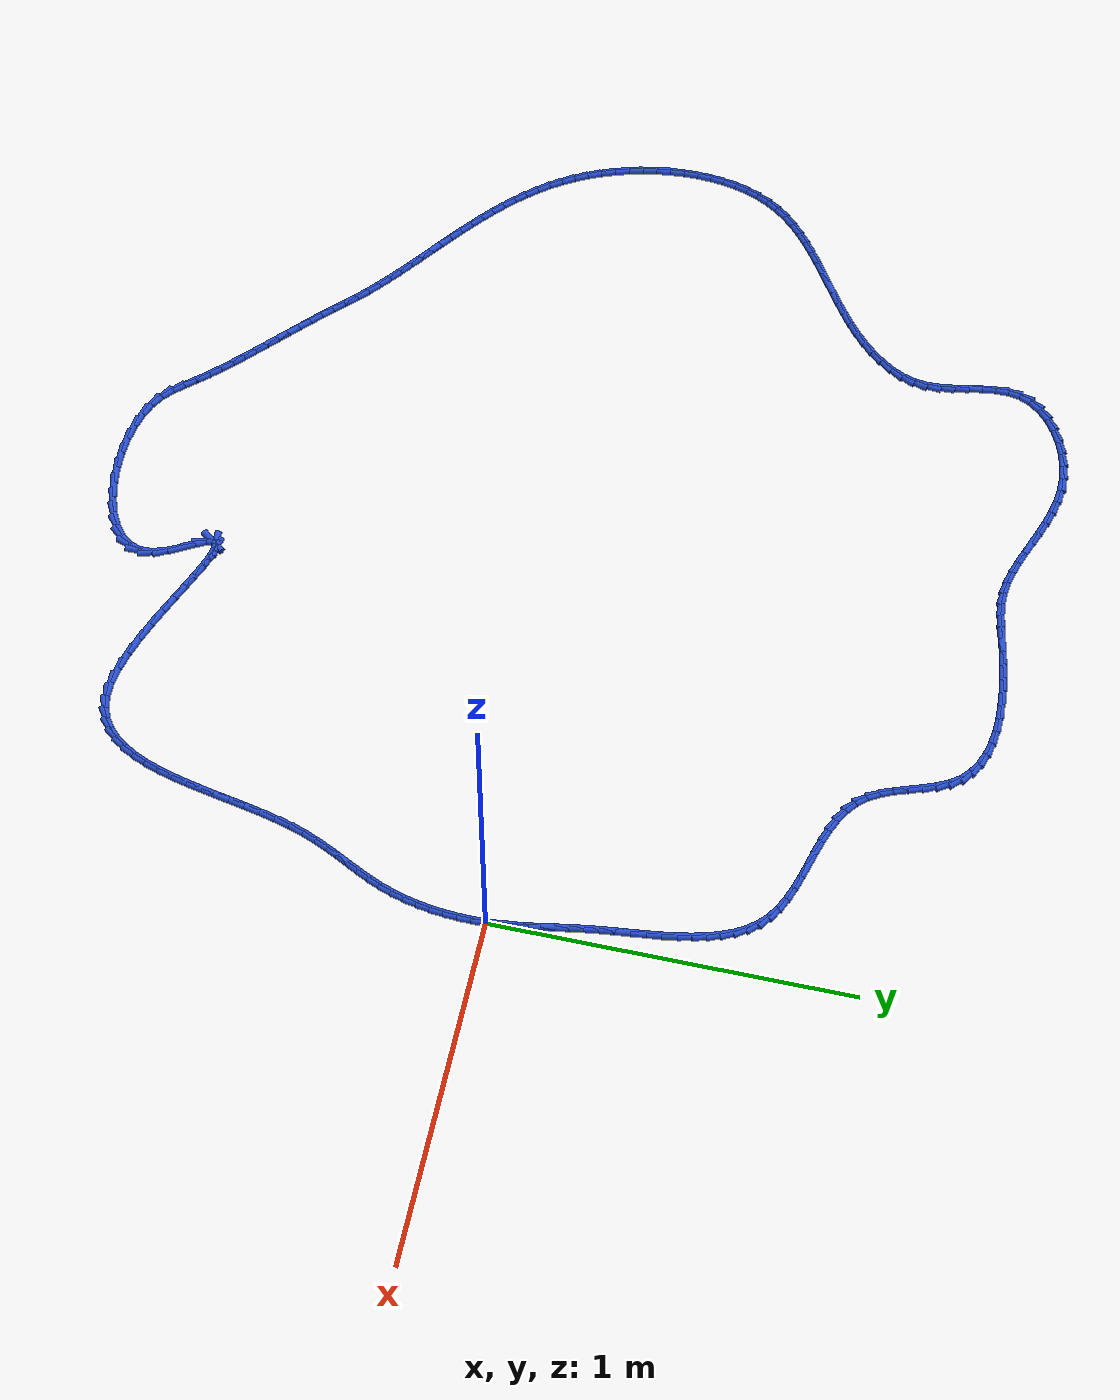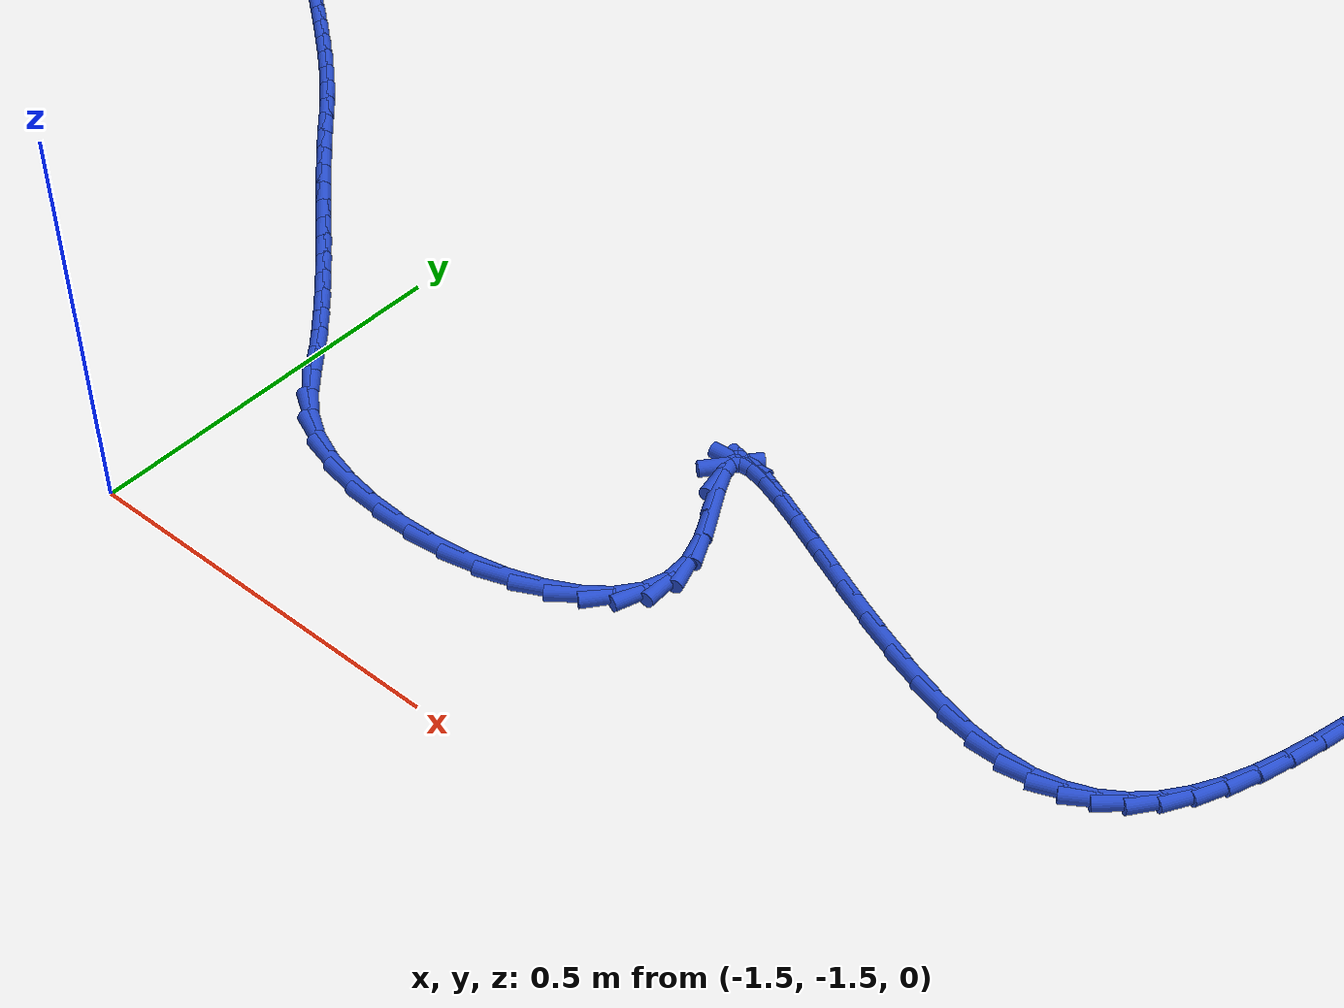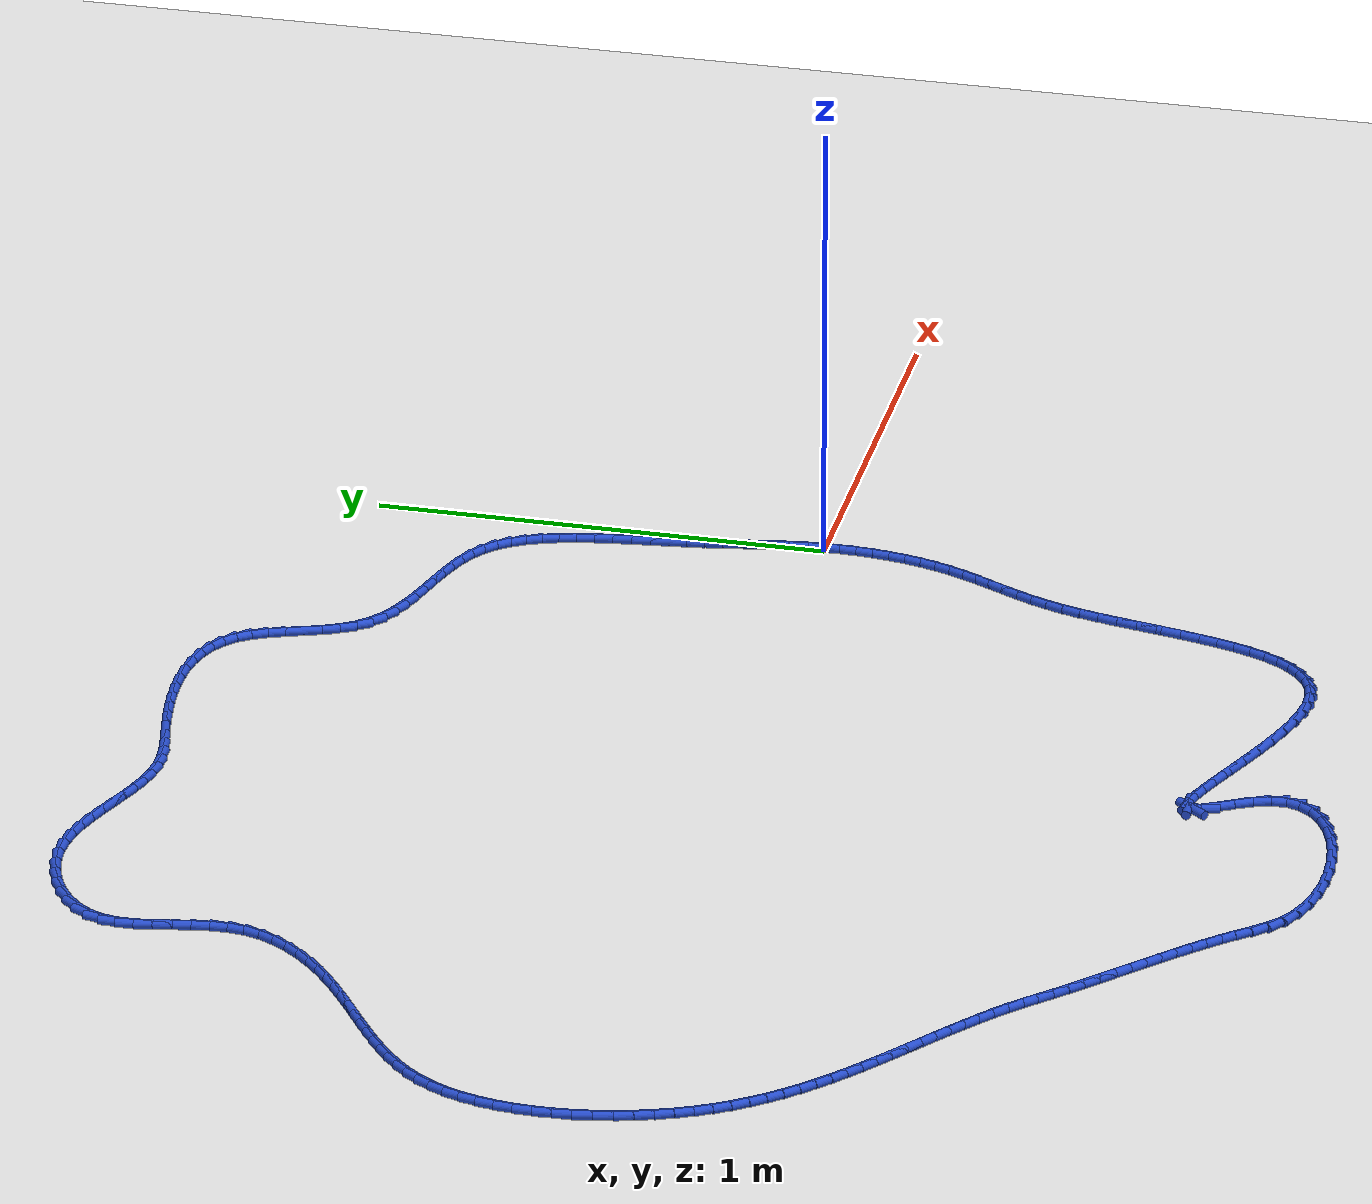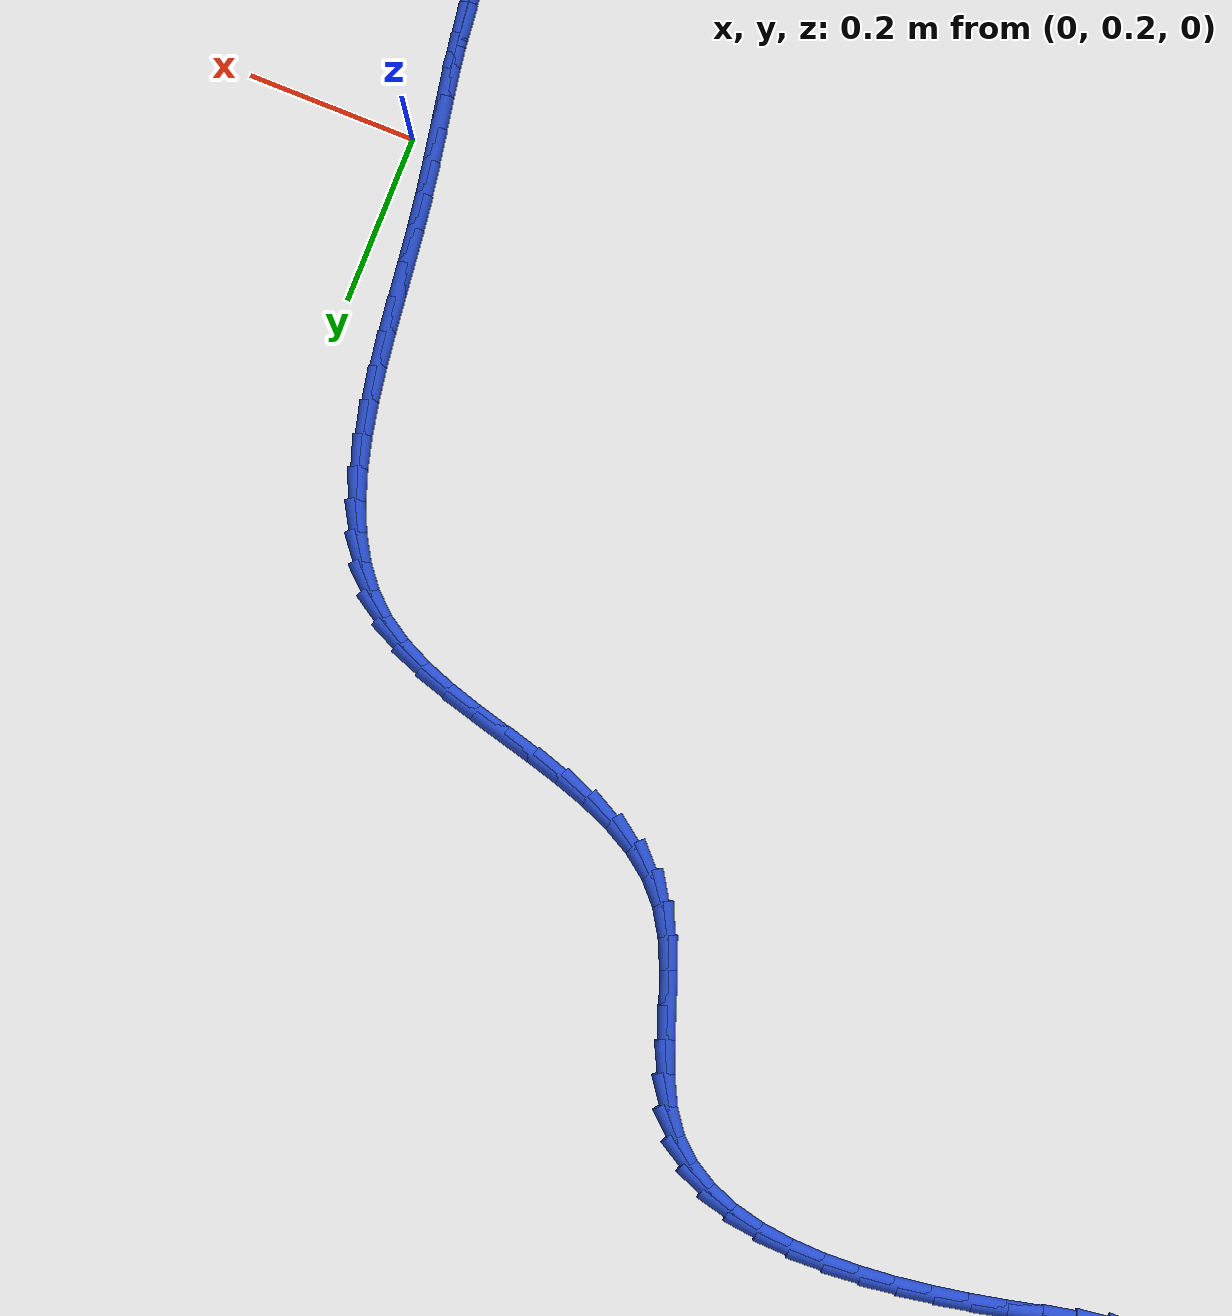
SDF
<sdf version="1.6">
 <world name="default">
  <light name="sun" type="directional">
   <pose>0 0 10 0 -0 0</pose>
   <diffuse>0.8 0.8 0.8 1</diffuse>
   <specular>0.2 0.2 0.2 1</specular>
   <attenuation>
    <range>1000</range>
    <constant>0.9</constant>
    <linear>0.01</linear>
    <quadratic>0.001</quadratic>
   </attenuation>
   <direction>-0.5 0.1 -0.9</direction>
  </light>
  <model name="ground_plane">
   <static>1</static>
   <link name="link">
    <collision name="collision">
     <geometry><plane><normal>0 0 1</normal><size>100 100</size></plane></geometry>
     <surface><friction><ode><mu>100</mu><mu2>50</mu2></ode></friction></surface>
    </collision>
    <visual name="visual">
     <cast_shadows>0</cast_shadows>
     <geometry><plane><normal>0 0 1</normal><size>100 100</size></plane></geometry>
     <material>
      <script><uri>file://media/materials/scripts/gazebo.material</uri><name>Gazebo/WhiteGlow</name></script>
     </material>
    </visual>
   </link>
  </model>
  <gravity>0 0 -9.8</gravity>
  <magnetic_field>6e-06 2.3e-05 -4.2e-05</magnetic_field>
  <atmosphere type="adiabatic"/>
  <physics name="default_physics" default="0" type="ode">
   <max_step_size>0.001</max_step_size>
   <real_time_factor>1</real_time_factor>
   <real_time_update_rate>1000</real_time_update_rate>
  </physics>
  <scene><ambient>0.4 0.4 0.4 1</ambient><background>0.7 0.7 0.7 1</background><shadows>1</shadows></scene>
  <spherical_coordinates>
   <surface_model>EARTH_WGS84</surface_model>
   <latitude_deg>0</latitude_deg>
   <longitude_deg>0</longitude_deg>
   <elevation>0</elevation>
   <heading_deg>0</heading_deg>
  </spherical_coordinates>
  <model name="line">
   <link name="link_0">
    <pose>-6.938893903907228e-18 -6.938893903907228e-18 0.01 0 1.57 -1.4983998689874092</pose>
    <collision name="collision">
     <geometry><cylinder><radius>0.01</radius><length>0.08</length></cylinder></geometry>
    </collision>
    <visual name="visual">
     <material>
      <script><name>Gazebo/Blue</name><uri>file://media/materials/scripts/gazebo.material</uri></script>
     </material>
     <geometry><cylinder><radius>0.01</radius><length>0.08</length></cylinder></geometry>
    </visual>
   </link>
   <link name="link_1">
    <pose>-0.002663180937082676 0.036721776100140734 0.01 0 1.57 -1.4579496935638216</pose>
    <collision name="collision">
     <geometry><cylinder><radius>0.01</radius><length>0.08</length></cylinder></geometry>
    </collision>
    <visual name="visual">
     <material>
      <script><name>Gazebo/Blue</name><uri>file://media/materials/scripts/gazebo.material</uri></script>
     </material>
     <geometry><cylinder><radius>0.01</radius><length>0.08</length></cylinder></geometry>
    </visual>
   </link>
   <link name="link_2">
    <pose>-0.006778611962420478 0.07303608100309464 0.01 0 1.57 -1.4274380562315656</pose>
    <collision name="collision">
     <geometry><cylinder><radius>0.01</radius><length>0.08</length></cylinder></geometry>
    </collision>
    <visual name="visual">
     <material>
      <script><name>Gazebo/Blue</name><uri>file://media/materials/scripts/gazebo.material</uri></script>
     </material>
     <geometry><cylinder><radius>0.01</radius><length>0.08</length></cylinder></geometry>
    </visual>
   </link>
   <link name="link_3">
    <pose>-0.011997254429461144 0.10918916024557128 0.01 0 1.57 -1.4074435517171158</pose>
    <collision name="collision">
     <geometry><cylinder><radius>0.01</radius><length>0.08</length></cylinder></geometry>
    </collision>
    <visual name="visual">
     <material>
      <script><name>Gazebo/Blue</name><uri>file://media/materials/scripts/gazebo.material</uri></script>
     </material>
     <geometry><cylinder><radius>0.01</radius><length>0.08</length></cylinder></geometry>
    </visual>
   </link>
   <link name="link_4">
    <pose>-0.01797006969165242 0.1454272593642804 0.01 0 1.57 -1.3981261967314953</pose>
    <collision name="collision">
     <geometry><cylinder><radius>0.01</radius><length>0.08</length></cylinder></geometry>
    </collision>
    <visual name="visual">
     <material>
      <script><name>Gazebo/Blue</name><uri>file://media/materials/scripts/gazebo.material</uri></script>
     </material>
     <geometry><cylinder><radius>0.01</radius><length>0.08</length></cylinder></geometry>
    </visual>
   </link>
   <link name="link_5">
    <pose>-0.024348019102442036 0.18199662389593138 0.01 0 1.57 -1.3992923194561482</pose>
    <collision name="collision">
     <geometry><cylinder><radius>0.01</radius><length>0.08</length></cylinder></geometry>
    </collision>
    <visual name="visual">
     <material>
      <script><name>Gazebo/Blue</name><uri>file://media/materials/scripts/gazebo.material</uri></script>
     </material>
     <geometry><cylinder><radius>0.01</radius><length>0.08</length></cylinder></geometry>
    </visual>
   </link>
   <link name="link_6">
    <pose>-0.0307820640152777 0.21914349937723393 0.01 0 1.57 -1.4104518432613529</pose>
    <collision name="collision">
     <geometry><cylinder><radius>0.01</radius><length>0.08</length></cylinder></geometry>
    </collision>
    <visual name="visual">
     <material>
      <script><name>Gazebo/Blue</name><uri>file://media/materials/scripts/gazebo.material</uri></script>
     </material>
     <geometry><cylinder><radius>0.01</radius><length>0.08</length></cylinder></geometry>
    </visual>
   </link>
   <link name="link_7">
    <pose>-0.03692316578360721 0.2571141313448977 0.01 0 1.57 -1.4306825054110668</pose>
    <collision name="collision">
     <geometry><cylinder><radius>0.01</radius><length>0.08</length></cylinder></geometry>
    </collision>
    <visual name="visual">
     <material>
      <script><name>Gazebo/Blue</name><uri>file://media/materials/scripts/gazebo.material</uri></script>
     </material>
     <geometry><cylinder><radius>0.01</radius><length>0.08</length></cylinder></geometry>
    </visual>
   </link>
   <link name="link_8">
    <pose>-0.0424285925186946 0.29614919685629043 0.01 0 1.57 -1.4508441233355336</pose>
    <collision name="collision">
     <geometry><cylinder><radius>0.01</radius><length>0.08</length></cylinder></geometry>
    </collision>
    <visual name="visual">
     <material>
      <script><name>Gazebo/Blue</name><uri>file://media/materials/scripts/gazebo.material</uri></script>
     </material>
     <geometry><cylinder><radius>0.01</radius><length>0.08</length></cylinder></geometry>
    </visual>
   </link>
   <link name="link_9">
    <pose>-0.04725858529024402 0.33622186647664826 0.01 0 1.57 -1.4595823480422738</pose>
    <collision name="collision">
     <geometry><cylinder><radius>0.01</radius><length>0.08</length></cylinder></geometry>
    </collision>
    <visual name="visual">
     <material>
      <script><name>Gazebo/Blue</name><uri>file://media/materials/scripts/gazebo.material</uri></script>
     </material>
     <geometry><cylinder><radius>0.01</radius><length>0.08</length></cylinder></geometry>
    </visual>
   </link>
   <link name="link_10">
    <pose>-0.051804100409577156 0.3769250156980553 0.01 0 1.57 -1.45674258455282</pose>
    <collision name="collision">
     <geometry><cylinder><radius>0.01</radius><length>0.08</length></cylinder></geometry>
    </collision>
    <visual name="visual">
     <material>
      <script><name>Gazebo/Blue</name><uri>file://media/materials/scripts/gazebo.material</uri></script>
     </material>
     <geometry><cylinder><radius>0.01</radius><length>0.08</length></cylinder></geometry>
    </visual>
   </link>
   <link name="link_11">
    <pose>-0.056488944772962214 0.41782251496611034 0.01 0 1.57 -1.4424227474310363</pose>
    <collision name="collision">
     <geometry><cylinder><radius>0.01</radius><length>0.08</length></cylinder></geometry>
    </collision>
    <visual name="visual">
     <material>
      <script><name>Gazebo/Blue</name><uri>file://media/materials/scripts/gazebo.material</uri></script>
     </material>
     <geometry><cylinder><radius>0.01</radius><length>0.08</length></cylinder></geometry>
    </visual>
   </link>
   <link name="link_12">
    <pose>-0.06173692527666738 0.45847823472641197 0.01 0 1.57 -1.4160830722713165</pose>
    <collision name="collision">
     <geometry><cylinder><radius>0.01</radius><length>0.08</length></cylinder></geometry>
    </collision>
    <visual name="visual">
     <material>
      <script><name>Gazebo/Blue</name><uri>file://media/materials/scripts/gazebo.material</uri></script>
     </material>
     <geometry><cylinder><radius>0.01</radius><length>0.08</length></cylinder></geometry>
    </visual>
   </link>
   <link name="link_13">
    <pose>-0.06797184881696085 0.4984560454245588 0.01 0 1.57 -1.3765468768446876</pose>
    <collision name="collision">
     <geometry><cylinder><radius>0.01</radius><length>0.08</length></cylinder></geometry>
    </collision>
    <visual name="visual">
     <material>
      <script><name>Gazebo/Blue</name><uri>file://media/materials/scripts/gazebo.material</uri></script>
     </material>
     <geometry><cylinder><radius>0.01</radius><length>0.08</length></cylinder></geometry>
    </visual>
   </link>
   <link name="link_14">
    <pose>-0.07561752229011076 0.5373198175061492 0.01 0 1.57 -1.321991691514747</pose>
    <collision name="collision">
     <geometry><cylinder><radius>0.01</radius><length>0.08</length></cylinder></geometry>
    </collision>
    <visual name="visual">
     <material>
      <script><name>Gazebo/Blue</name><uri>file://media/materials/scripts/gazebo.material</uri></script>
     </material>
     <geometry><cylinder><radius>0.01</radius><length>0.08</length></cylinder></geometry>
    </visual>
   </link>
   <link name="link_15">
    <pose>-0.08509775259238536 0.574633421416782 0.01 0 1.57 -1.2499931354912268</pose>
    <collision name="collision">
     <geometry><cylinder><radius>0.01</radius><length>0.08</length></cylinder></geometry>
    </collision>
    <visual name="visual">
     <material>
      <script><name>Gazebo/Blue</name><uri>file://media/materials/scripts/gazebo.material</uri></script>
     </material>
     <geometry><cylinder><radius>0.01</radius><length>0.08</length></cylinder></geometry>
    </visual>
   </link>
   <link name="link_16">
    <pose>-0.0968363466200528 0.6099607276020559 0.01 0 1.57 -1.157751414140631</pose>
    <collision name="collision">
     <geometry><cylinder><radius>0.01</radius><length>0.08</length></cylinder></geometry>
    </collision>
    <visual name="visual">
     <material>
      <script><name>Gazebo/Blue</name><uri>file://media/materials/scripts/gazebo.material</uri></script>
     </material>
     <geometry><cylinder><radius>0.01</radius><length>0.08</length></cylinder></geometry>
    </visual>
   </link>
   <link name="link_17">
    <pose>-0.11125711126938126 0.6428656065075691 0.01 0 1.57 -1.0427288075779644</pose>
    <collision name="collision">
     <geometry><cylinder><radius>0.01</radius><length>0.08</length></cylinder></geometry>
    </collision>
    <visual name="visual">
     <material>
      <script><name>Gazebo/Blue</name><uri>file://media/materials/scripts/gazebo.material</uri></script>
     </material>
     <geometry><cylinder><radius>0.01</radius><length>0.08</length></cylinder></geometry>
    </visual>
   </link>
   <link name="link_18">
    <pose>-0.12878385343663895 0.6729119285789205 0.01 0 1.57 -0.9039636330388187</pose>
    <collision name="collision">
     <geometry><cylinder><radius>0.01</radius><length>0.08</length></cylinder></geometry>
    </collision>
    <visual name="visual">
     <material>
      <script><name>Gazebo/Blue</name><uri>file://media/materials/scripts/gazebo.material</uri></script>
     </material>
     <geometry><cylinder><radius>0.01</radius><length>0.08</length></cylinder></geometry>
    </visual>
   </link>
   <link name="link_19">
    <pose>-0.14984038001809402 0.6996635642617084 0.01 0 1.57 -0.7440048097767803</pose>
    <collision name="collision">
     <geometry><cylinder><radius>0.01</radius><length>0.08</length></cylinder></geometry>
    </collision>
    <visual name="visual">
     <material>
      <script><name>Gazebo/Blue</name><uri>file://media/materials/scripts/gazebo.material</uri></script>
     </material>
     <geometry><cylinder><radius>0.01</radius><length>0.08</length></cylinder></geometry>
    </visual>
   </link>
   <link name="link_20">
    <pose>-0.17485049777258305 0.7226843841394761 0.01 0 1.57 -0.5787754051907241</pose>
    <collision name="collision">
     <geometry><cylinder><radius>0.01</radius><length>0.08</length></cylinder></geometry>
    </collision>
    <visual name="visual">
     <material>
      <script><name>Gazebo/Blue</name><uri>file://media/materials/scripts/gazebo.material</uri></script>
     </material>
     <geometry><cylinder><radius>0.01</radius><length>0.08</length></cylinder></geometry>
    </visual>
   </link>
   <link name="link_21">
    <pose>-0.20402771044870213 0.7417493468965731 0.01 0 1.57 -0.4473238556022628</pose>
    <collision name="collision">
     <geometry><cylinder><radius>0.01</radius><length>0.08</length></cylinder></geometry>
    </collision>
    <visual name="visual">
     <material>
      <script><name>Gazebo/Blue</name><uri>file://media/materials/scripts/gazebo.material</uri></script>
     </material>
     <geometry><cylinder><radius>0.01</radius><length>0.08</length></cylinder></geometry>
    </visual>
   </link>
   <link name="link_22">
    <pose>-0.23676611170035805 0.757455880284583 0.01 0 1.57 -0.3547017166186103</pose>
    <collision name="collision">
     <geometry><cylinder><radius>0.01</radius><length>0.08</length></cylinder></geometry>
    </collision>
    <visual name="visual">
     <material>
      <script><name>Gazebo/Blue</name><uri>file://media/materials/scripts/gazebo.material</uri></script>
     </material>
     <geometry><cylinder><radius>0.01</radius><length>0.08</length></cylinder></geometry>
    </visual>
   </link>
   <link name="link_23">
    <pose>-0.27226025260397335 0.7706016995529387 0.01 0 1.57 -0.2951154553681825</pose>
    <collision name="collision">
     <geometry><cylinder><radius>0.01</radius><length>0.08</length></cylinder></geometry>
    </collision>
    <visual name="visual">
     <material>
      <script><name>Gazebo/Blue</name><uri>file://media/materials/scripts/gazebo.material</uri></script>
     </material>
     <geometry><cylinder><radius>0.01</radius><length>0.08</length></cylinder></geometry>
    </visual>
   </link>
   <link name="link_24">
    <pose>-0.3097046842359704 0.7819845199510725 0.01 0 1.57 -0.26367398483485727</pose>
    <collision name="collision">
     <geometry><cylinder><radius>0.01</radius><length>0.08</length></cylinder></geometry>
    </collision>
    <visual name="visual">
     <material>
      <script><name>Gazebo/Blue</name><uri>file://media/materials/scripts/gazebo.material</uri></script>
     </material>
     <geometry><cylinder><radius>0.01</radius><length>0.08</length></cylinder></geometry>
    </visual>
   </link>
   <link name="link_25">
    <pose>-0.3482939576727716 0.7924020567284175 0.01 0 1.57 -0.2574578265659017</pose>
    <collision name="collision">
     <geometry><cylinder><radius>0.01</radius><length>0.08</length></cylinder></geometry>
    </collision>
    <visual name="visual">
     <material>
      <script><name>Gazebo/Blue</name><uri>file://media/materials/scripts/gazebo.material</uri></script>
     </material>
     <geometry><cylinder><radius>0.01</radius><length>0.08</length></cylinder></geometry>
    </visual>
   </link>
   <link name="link_26">
    <pose>-0.3872226239907994 0.8026520251344057 0.01 0 1.57 -0.27567280079762935</pose>
    <collision name="collision">
     <geometry><cylinder><radius>0.01</radius><length>0.08</length></cylinder></geometry>
    </collision>
    <visual name="visual">
     <material>
      <script><name>Gazebo/Blue</name><uri>file://media/materials/scripts/gazebo.material</uri></script>
     </material>
     <geometry><cylinder><radius>0.01</radius><length>0.08</length></cylinder></geometry>
    </visual>
   </link>
   <link name="link_27">
    <pose>-0.42568523426647625 0.8135321404184703 0.01 0 1.57 -0.3195938715465448</pose>
    <collision name="collision">
     <geometry><cylinder><radius>0.01</radius><length>0.08</length></cylinder></geometry>
    </collision>
    <visual name="visual">
     <material>
      <script><name>Gazebo/Blue</name><uri>file://media/materials/scripts/gazebo.material</uri></script>
     </material>
     <geometry><cylinder><radius>0.01</radius><length>0.08</length></cylinder></geometry>
    </visual>
   </link>
   <link name="link_28">
    <pose>-0.4628763395762243 0.8258401178300435 0.01 0 1.57 -0.39242672985644594</pose>
    <collision name="collision">
     <geometry><cylinder><radius>0.01</radius><length>0.08</length></cylinder></geometry>
    </collision>
    <visual name="visual">
     <material>
      <script><name>Gazebo/Blue</name><uri>file://media/materials/scripts/gazebo.material</uri></script>
     </material>
     <geometry><cylinder><radius>0.01</radius><length>0.08</length></cylinder></geometry>
    </visual>
   </link>
   <link name="link_29">
    <pose>-0.4979904909964664 0.8403736726185582 0.01 0 1.57 -0.4987701275690292</pose>
    <collision name="collision">
     <geometry><cylinder><radius>0.01</radius><length>0.08</length></cylinder></geometry>
    </collision>
    <visual name="visual">
     <material>
      <script><name>Gazebo/Blue</name><uri>file://media/materials/scripts/gazebo.material</uri></script>
     </material>
     <geometry><cylinder><radius>0.01</radius><length>0.08</length></cylinder></geometry>
    </visual>
   </link>
   <link name="link_30">
    <pose>-0.530222239603625 0.8579305200334474 0.01 0 1.57 -0.6428266093174635</pose>
    <collision name="collision">
     <geometry><cylinder><radius>0.01</radius><length>0.08</length></cylinder></geometry>
    </collision>
    <visual name="visual">
     <material>
      <script><name>Gazebo/Blue</name><uri>file://media/materials/scripts/gazebo.material</uri></script>
     </material>
     <geometry><cylinder><radius>0.01</radius><length>0.08</length></cylinder></geometry>
    </visual>
   </link>
   <link name="link_31">
    <pose>-0.5587661364741221 0.8793083753241426 0.01 0 1.57 -0.8242538093117706</pose>
    <collision name="collision">
     <geometry><cylinder><radius>0.01</radius><length>0.08</length></cylinder></geometry>
    </collision>
    <visual name="visual">
     <material>
      <script><name>Gazebo/Blue</name><uri>file://media/materials/scripts/gazebo.material</uri></script>
     </material>
     <geometry><cylinder><radius>0.01</radius><length>0.08</length></cylinder></geometry>
    </visual>
   </link>
   <link name="link_32">
    <pose>-0.5828169219766167 0.9053047549811906 0.01 0 1.57 -1.0140825845502763</pose>
    <collision name="collision">
     <geometry><cylinder><radius>0.01</radius><length>0.08</length></cylinder></geometry>
    </collision>
    <visual name="visual">
     <material>
      <script><name>Gazebo/Blue</name><uri>file://media/materials/scripts/gazebo.material</uri></script>
     </material>
     <geometry><cylinder><radius>0.01</radius><length>0.08</length></cylinder></geometry>
    </visual>
   </link>
   <link name="link_33">
    <pose>-0.6020519942606182 0.9362103796270338 0.01 0 1.57 -1.1456336317526408</pose>
    <collision name="collision">
     <geometry><cylinder><radius>0.01</radius><length>0.08</length></cylinder></geometry>
    </collision>
    <visual name="visual">
     <material>
      <script><name>Gazebo/Blue</name><uri>file://media/materials/scripts/gazebo.material</uri></script>
     </material>
     <geometry><cylinder><radius>0.01</radius><length>0.08</length></cylinder></geometry>
    </visual>
   </link>
   <link name="link_34">
    <pose>-0.617674485148079 0.9707139330959419 0.01 0 1.57 -1.2159758097668745</pose>
    <collision name="collision">
     <geometry><cylinder><radius>0.01</radius><length>0.08</length></cylinder></geometry>
    </collision>
    <visual name="visual">
     <material>
      <script><name>Gazebo/Blue</name><uri>file://media/materials/scripts/gazebo.material</uri></script>
     </material>
     <geometry><cylinder><radius>0.01</radius><length>0.08</length></cylinder></geometry>
    </visual>
   </link>
   <link name="link_35">
    <pose>-0.6311882772888161 1.00718830761385 0.01 0 1.57 -1.2335736752910644</pose>
    <collision name="collision">
     <geometry><cylinder><radius>0.01</radius><length>0.08</length></cylinder></geometry>
    </collision>
    <visual name="visual">
     <material>
      <script><name>Gazebo/Blue</name><uri>file://media/materials/scripts/gazebo.material</uri></script>
     </material>
     <geometry><cylinder><radius>0.01</radius><length>0.08</length></cylinder></geometry>
    </visual>
   </link>
   <link name="link_36">
    <pose>-0.6440972533326463 1.0440063954066927 0.01 0 1.57 -1.2001740743552414</pose>
    <collision name="collision">
     <geometry><cylinder><radius>0.01</radius><length>0.08</length></cylinder></geometry>
    </collision>
    <visual name="visual">
     <material>
      <script><name>Gazebo/Blue</name><uri>file://media/materials/scripts/gazebo.material</uri></script>
     </material>
     <geometry><cylinder><radius>0.01</radius><length>0.08</length></cylinder></geometry>
    </visual>
   </link>
   <link name="link_37">
    <pose>-0.6579052959293871 1.0795410887004064 0.01 0 1.57 -1.1096310227361361</pose>
    <collision name="collision">
     <geometry><cylinder><radius>0.01</radius><length>0.08</length></cylinder></geometry>
    </collision>
    <visual name="visual">
     <material>
      <script><name>Gazebo/Blue</name><uri>file://media/materials/scripts/gazebo.material</uri></script>
     </material>
     <geometry><cylinder><radius>0.01</radius><length>0.08</length></cylinder></geometry>
    </visual>
   </link>
   <link name="link_38">
    <pose>-0.6741162877288543 1.1121652797209245 0.01 0 1.57 -0.9494790557066273</pose>
    <collision name="collision">
     <geometry><cylinder><radius>0.01</radius><length>0.08</length></cylinder></geometry>
    </collision>
    <visual name="visual">
     <material>
      <script><name>Gazebo/Blue</name><uri>file://media/materials/scripts/gazebo.material</uri></script>
     </material>
     <geometry><cylinder><radius>0.01</radius><length>0.08</length></cylinder></geometry>
    </visual>
   </link>
   <link name="link_39">
    <pose>-0.6942278910938241 1.140258053673404 0.01 0 1.57 -0.7386010818070715</pose>
    <collision name="collision">
     <geometry><cylinder><radius>0.01</radius><length>0.08</length></cylinder></geometry>
    </collision>
    <visual name="visual">
     <material>
      <script><name>Gazebo/Blue</name><uri>file://media/materials/scripts/gazebo.material</uri></script>
     </material>
     <geometry><cylinder><radius>0.01</radius><length>0.08</length></cylinder></geometry>
    </visual>
   </link>
   <link name="link_40">
    <pose>-0.7190625787228633 1.1628707212621319 0.01 0 1.57 -0.5400326307048426</pose>
    <collision name="collision">
     <geometry><cylinder><radius>0.01</radius><length>0.08</length></cylinder></geometry>
    </collision>
    <visual name="visual">
     <material>
      <script><name>Gazebo/Blue</name><uri>file://media/materials/scripts/gazebo.material</uri></script>
     </material>
     <geometry><cylinder><radius>0.01</radius><length>0.08</length></cylinder></geometry>
    </visual>
   </link>
   <link name="link_41">
    <pose>-0.7481712323672101 1.1803206016991812 0.01 0 1.57 -0.37067250426464926</pose>
    <collision name="collision">
     <geometry><cylinder><radius>0.01</radius><length>0.08</length></cylinder></geometry>
    </collision>
    <visual name="visual">
     <material>
      <script><name>Gazebo/Blue</name><uri>file://media/materials/scripts/gazebo.material</uri></script>
     </material>
     <geometry><cylinder><radius>0.01</radius><length>0.08</length></cylinder></geometry>
    </visual>
   </link>
   <link name="link_42">
    <pose>-0.7809640320442479 1.1930650982326867 0.01 0 1.57 -0.23247602954185473</pose>
    <collision name="collision">
     <geometry><cylinder><radius>0.01</radius><length>0.08</length></cylinder></geometry>
    </collision>
    <visual name="visual">
     <material>
      <script><name>Gazebo/Blue</name><uri>file://media/materials/scripts/gazebo.material</uri></script>
     </material>
     <geometry><cylinder><radius>0.01</radius><length>0.08</length></cylinder></geometry>
    </visual>
   </link>
   <link name="link_43">
    <pose>-0.816851157771359 1.201561614110782 0.01 0 1.57 -0.12196875474758288</pose>
    <collision name="collision">
     <geometry><cylinder><radius>0.01</radius><length>0.08</length></cylinder></geometry>
    </collision>
    <visual name="visual">
     <material>
      <script><name>Gazebo/Blue</name><uri>file://media/materials/scripts/gazebo.material</uri></script>
     </material>
     <geometry><cylinder><radius>0.01</radius><length>0.08</length></cylinder></geometry>
    </visual>
   </link>
   <link name="link_44">
    <pose>-0.8552427895659267 1.2062675525816027 0.01 0 1.57 -0.03404513152766908</pose>
    <collision name="collision">
     <geometry><cylinder><radius>0.01</radius><length>0.08</length></cylinder></geometry>
    </collision>
    <visual name="visual">
     <material>
      <script><name>Gazebo/Blue</name><uri>file://media/materials/scripts/gazebo.material</uri></script>
     </material>
     <geometry><cylinder><radius>0.01</radius><length>0.08</length></cylinder></geometry>
    </visual>
   </link>
   <link name="link_45">
    <pose>-0.895549107445334 1.207640316893283 0.01 0 1.57 0.036087229566069474</pose>
    <collision name="collision">
     <geometry><cylinder><radius>0.01</radius><length>0.08</length></cylinder></geometry>
    </collision>
    <visual name="visual">
     <material>
      <script><name>Gazebo/Blue</name><uri>file://media/materials/scripts/gazebo.material</uri></script>
     </material>
     <geometry><cylinder><radius>0.01</radius><length>0.08</length></cylinder></geometry>
    </visual>
   </link>
   <link name="link_46">
    <pose>-0.937180291426963 1.2061373102939568 0.01 0 1.57 0.09229598944925757</pose>
    <collision name="collision">
     <geometry><cylinder><radius>0.01</radius><length>0.08</length></cylinder></geometry>
    </collision>
    <visual name="visual">
     <material>
      <script><name>Gazebo/Blue</name><uri>file://media/materials/scripts/gazebo.material</uri></script>
     </material>
     <geometry><cylinder><radius>0.01</radius><length>0.08</length></cylinder></geometry>
    </visual>
   </link>
   <link name="link_47">
    <pose>-0.9795465215281973 1.2022159360317597 0.01 0 1.57 0.13749757610627572</pose>
    <collision name="collision">
     <geometry><cylinder><radius>0.01</radius><length>0.08</length></cylinder></geometry>
    </collision>
    <visual name="visual">
     <material>
      <script><name>Gazebo/Blue</name><uri>file://media/materials/scripts/gazebo.material</uri></script>
     </material>
     <geometry><cylinder><radius>0.01</radius><length>0.08</length></cylinder></geometry>
    </visual>
   </link>
   <link name="link_48">
    <pose>-1.0220579777664203 1.1963335973548257 0.01 0 1.57 0.1738037674681937</pose>
    <collision name="collision">
     <geometry><cylinder><radius>0.01</radius><length>0.08</length></cylinder></geometry>
    </collision>
    <visual name="visual">
     <material>
      <script><name>Gazebo/Blue</name><uri>file://media/materials/scripts/gazebo.material</uri></script>
     </material>
     <geometry><cylinder><radius>0.01</radius><length>0.08</length></cylinder></geometry>
    </visual>
   </link>
   <link name="link_49">
    <pose>-1.0641248401590138 1.1889476975112894 0.01 0 1.57 0.20267580263170223</pose>
    <collision name="collision">
     <geometry><cylinder><radius>0.01</radius><length>0.08</length></cylinder></geometry>
    </collision>
    <visual name="visual">
     <material>
      <script><name>Gazebo/Blue</name><uri>file://media/materials/scripts/gazebo.material</uri></script>
     </material>
     <geometry><cylinder><radius>0.01</radius><length>0.08</length></cylinder></geometry>
    </visual>
   </link>
   <link name="link_50">
    <pose>-1.1051572887233614 1.1805156397492853 0.01 0 1.57 0.22408980094221054</pose>
    <collision name="collision">
     <geometry><cylinder><radius>0.01</radius><length>0.08</length></cylinder></geometry>
    </collision>
    <visual name="visual">
     <material>
      <script><name>Gazebo/Blue</name><uri>file://media/materials/scripts/gazebo.material</uri></script>
     </material>
     <geometry><cylinder><radius>0.01</radius><length>0.08</length></cylinder></geometry>
    </visual>
   </link>
   <link name="link_51">
    <pose>-1.1446056983608281 1.171524649327541 0.01 0 1.57 0.22513276359493178</pose>
    <collision name="collision">
     <geometry><cylinder><radius>0.01</radius><length>0.08</length></cylinder></geometry>
    </collision>
    <visual name="visual">
     <material>
      <script><name>Gazebo/Blue</name><uri>file://media/materials/scripts/gazebo.material</uri></script>
     </material>
     <geometry><cylinder><radius>0.01</radius><length>0.08</length></cylinder></geometry>
    </visual>
   </link>
   <link name="link_52">
    <pose>-1.182452971487688 1.1628570525628648 0.01 0 1.57 0.19373255120533125</pose>
    <collision name="collision">
     <geometry><cylinder><radius>0.01</radius><length>0.08</length></cylinder></geometry>
    </collision>
    <visual name="visual">
     <material>
      <script><name>Gazebo/Blue</name><uri>file://media/materials/scripts/gazebo.material</uri></script>
     </material>
     <geometry><cylinder><radius>0.01</radius><length>0.08</length></cylinder></geometry>
    </visual>
   </link>
   <link name="link_53">
    <pose>-1.2190593405492742 1.1556751303087824 0.01 0 1.57 0.1260443402359267</pose>
    <collision name="collision">
     <geometry><cylinder><radius>0.01</radius><length>0.08</length></cylinder></geometry>
    </collision>
    <visual name="visual">
     <material>
      <script><name>Gazebo/Blue</name><uri>file://media/materials/scripts/gazebo.material</uri></script>
     </material>
     <geometry><cylinder><radius>0.01</radius><length>0.08</length></cylinder></geometry>
    </visual>
   </link>
   <link name="link_54">
    <pose>-1.254793033872802 1.151147095847294 0.01 0 1.57 0.020079067519532236</pose>
    <collision name="collision">
     <geometry><cylinder><radius>0.01</radius><length>0.08</length></cylinder></geometry>
    </collision>
    <visual name="visual">
     <material>
      <script><name>Gazebo/Blue</name><uri>file://media/materials/scripts/gazebo.material</uri></script>
     </material>
     <geometry><cylinder><radius>0.01</radius><length>0.08</length></cylinder></geometry>
    </visual>
   </link>
   <link name="link_55">
    <pose>-1.290022089403081 1.1504396341845708 0.01 0 1.57 -0.10632945192606161</pose>
    <collision name="collision">
     <geometry><cylinder><radius>0.01</radius><length>0.08</length></cylinder></geometry>
    </collision>
    <visual name="visual">
     <material>
      <script><name>Gazebo/Blue</name><uri>file://media/materials/scripts/gazebo.material</uri></script>
     </material>
     <geometry><cylinder><radius>0.01</radius><length>0.08</length></cylinder></geometry>
    </visual>
   </link>
   <link name="link_56">
    <pose>-1.325047087588335 1.154177921976757 0.01 0 1.57 -0.21056906209801196</pose>
    <collision name="collision">
     <geometry><cylinder><radius>0.01</radius><length>0.08</length></cylinder></geometry>
    </collision>
    <visual name="visual">
     <material>
      <script><name>Gazebo/Blue</name><uri>file://media/materials/scripts/gazebo.material</uri></script>
     </material>
     <geometry><cylinder><radius>0.01</radius><length>0.08</length></cylinder></geometry>
    </visual>
   </link>
   <link name="link_57">
    <pose>-1.36000192263279 1.161649078621337 0.01 0 1.57 -0.2859449568787356</pose>
    <collision name="collision">
     <geometry><cylinder><radius>0.01</radius><length>0.08</length></cylinder></geometry>
    </collision>
    <visual name="visual">
     <material>
      <script><name>Gazebo/Blue</name><uri>file://media/materials/scripts/gazebo.material</uri></script>
     </material>
     <geometry><cylinder><radius>0.01</radius><length>0.08</length></cylinder></geometry>
    </visual>
   </link>
   <link name="link_58">
    <pose>-1.3949951935207343 1.1719371686515603 0.01 0 1.57 -0.3338829245666316</pose>
    <collision name="collision">
     <geometry><cylinder><radius>0.01</radius><length>0.08</length></cylinder></geometry>
    </collision>
    <visual name="visual">
     <material>
      <script><name>Gazebo/Blue</name><uri>file://media/materials/scripts/gazebo.material</uri></script>
     </material>
     <geometry><cylinder><radius>0.01</radius><length>0.08</length></cylinder></geometry>
    </visual>
   </link>
   <link name="link_59">
    <pose>-1.4301354992364586 1.1841262566006776 0.01 0 1.57 -0.3563082021203419</pose>
    <collision name="collision">
     <geometry><cylinder><radius>0.01</radius><length>0.08</length></cylinder></geometry>
    </collision>
    <visual name="visual">
     <material>
      <script><name>Gazebo/Blue</name><uri>file://media/materials/scripts/gazebo.material</uri></script>
     </material>
     <geometry><cylinder><radius>0.01</radius><length>0.08</length></cylinder></geometry>
    </visual>
   </link>
   <link name="link_60">
    <pose>-1.4655314387642513 1.197300407001937 0.01 0 1.57 -0.3546753832581788</pose>
    <collision name="collision">
     <geometry><cylinder><radius>0.01</radius><length>0.08</length></cylinder></geometry>
    </collision>
    <visual name="visual">
     <material>
      <script><name>Gazebo/Blue</name><uri>file://media/materials/scripts/gazebo.material</uri></script>
     </material>
     <geometry><cylinder><radius>0.01</radius><length>0.08</length></cylinder></geometry>
    </visual>
   </link>
   <link name="link_61">
    <pose>-1.5012916110884034 1.2105436843885897 0.01 0 1.57 -0.32964831173904147</pose>
    <collision name="collision">
     <geometry><cylinder><radius>0.01</radius><length>0.08</length></cylinder></geometry>
    </collision>
    <visual name="visual">
     <material>
      <script><name>Gazebo/Blue</name><uri>file://media/materials/scripts/gazebo.material</uri></script>
     </material>
     <geometry><cylinder><radius>0.01</radius><length>0.08</length></cylinder></geometry>
    </visual>
   </link>
   <link name="link_62">
    <pose>-1.537524615193203 1.2229401532938844 0.01 0 1.57 -0.28119318542623895</pose>
    <collision name="collision">
     <geometry><cylinder><radius>0.01</radius><length>0.08</length></cylinder></geometry>
    </collision>
    <visual name="visual">
     <material>
      <script><name>Gazebo/Blue</name><uri>file://media/materials/scripts/gazebo.material</uri></script>
     </material>
     <geometry><cylinder><radius>0.01</radius><length>0.08</length></cylinder></geometry>
    </visual>
   </link>
   <link name="link_63">
    <pose>-1.5743390500629404 1.2335738782510712 0.01 0 1.57 -0.20901153859722285</pose>
    <collision name="collision">
     <geometry><cylinder><radius>0.01</radius><length>0.08</length></cylinder></geometry>
    </collision>
    <visual name="visual">
     <material>
      <script><name>Gazebo/Blue</name><uri>file://media/materials/scripts/gazebo.material</uri></script>
     </material>
     <geometry><cylinder><radius>0.01</radius><length>0.08</length></cylinder></geometry>
    </visual>
   </link>
   <link name="link_64">
    <pose>-1.6118435146819046 1.2415289237933995 0.01 0 1.57 -0.11335218515583197</pose>
    <collision name="collision">
     <geometry><cylinder><radius>0.01</radius><length>0.08</length></cylinder></geometry>
    </collision>
    <visual name="visual">
     <material>
      <script><name>Gazebo/Blue</name><uri>file://media/materials/scripts/gazebo.material</uri></script>
     </material>
     <geometry><cylinder><radius>0.01</radius><length>0.08</length></cylinder></geometry>
    </visual>
   </link>
   <link name="link_65">
    <pose>-1.6501466080343854 1.245889354454119 0.01 0 1.57 0.0038285571263841764</pose>
    <collision name="collision">
     <geometry><cylinder><radius>0.01</radius><length>0.08</length></cylinder></geometry>
    </collision>
    <visual name="visual">
     <material>
      <script><name>Gazebo/Blue</name><uri>file://media/materials/scripts/gazebo.material</uri></script>
     </material>
     <geometry><cylinder><radius>0.01</radius><length>0.08</length></cylinder></geometry>
    </visual>
   </link>
   <link name="link_66">
    <pose>-1.689356929104673 1.2457392347664795 0.01 0 1.57 0.1337514484782975</pose>
    <collision name="collision">
     <geometry><cylinder><radius>0.01</radius><length>0.08</length></cylinder></geometry>
    </collision>
    <visual name="visual">
     <material>
      <script><name>Gazebo/Blue</name><uri>file://media/materials/scripts/gazebo.material</uri></script>
     </material>
     <geometry><cylinder><radius>0.01</radius><length>0.08</length></cylinder></geometry>
    </visual>
   </link>
   <link name="link_67">
    <pose>-1.7293963523306966 1.2403517390886074 0.01 0 1.57 0.25645817553809747</pose>
    <collision name="collision">
     <geometry><cylinder><radius>0.01</radius><length>0.08</length></cylinder></geometry>
    </collision>
    <visual name="visual">
     <material>
      <script><name>Gazebo/Blue</name><uri>file://media/materials/scripts/gazebo.material</uri></script>
     </material>
     <geometry><cylinder><radius>0.01</radius><length>0.08</length></cylinder></geometry>
    </visual>
   </link>
   <link name="link_68">
    <pose>-1.7693138843526466 1.2298840598661762 0.01 0 1.57 0.37371139468720943</pose>
    <collision name="collision">
     <geometry><cylinder><radius>0.01</radius><length>0.08</length></cylinder></geometry>
    </collision>
    <visual name="visual">
     <material>
      <script><name>Gazebo/Blue</name><uri>file://media/materials/scripts/gazebo.material</uri></script>
     </material>
     <geometry><cylinder><radius>0.01</radius><length>0.08</length></cylinder></geometry>
    </visual>
   </link>
   <link name="link_69">
    <pose>-1.8079036855508113 1.2147514912916275 0.01 0 1.57 0.4932370815236531</pose>
    <collision name="collision">
     <geometry><cylinder><radius>0.01</radius><length>0.08</length></cylinder></geometry>
    </collision>
    <visual name="visual">
     <material>
      <script><name>Gazebo/Blue</name><uri>file://media/materials/scripts/gazebo.material</uri></script>
     </material>
     <geometry><cylinder><radius>0.01</radius><length>0.08</length></cylinder></geometry>
    </visual>
   </link>
   <link name="link_70">
    <pose>-1.8439598857299757 1.1953693585234921 0.01 0 1.57 0.6229692006363593</pose>
    <collision name="collision">
     <geometry><cylinder><radius>0.01</radius><length>0.08</length></cylinder></geometry>
    </collision>
    <visual name="visual">
     <material>
      <script><name>Gazebo/Blue</name><uri>file://media/materials/scripts/gazebo.material</uri></script>
     </material>
     <geometry><cylinder><radius>0.01</radius><length>0.08</length></cylinder></geometry>
    </visual>
   </link>
   <link name="link_71">
    <pose>-1.876276614694923 1.1721529867203007 0.01 0 1.57 0.7717691754533109</pose>
    <collision name="collision">
     <geometry><cylinder><radius>0.01</radius><length>0.08</length></cylinder></geometry>
    </collision>
    <visual name="visual">
     <material>
      <script><name>Gazebo/Blue</name><uri>file://media/materials/scripts/gazebo.material</uri></script>
     </material>
     <geometry><cylinder><radius>0.01</radius><length>0.08</length></cylinder></geometry>
    </visual>
   </link>
   <link name="link_72">
    <pose>-1.9036480022504367 1.145517701040583 0.01 0 1.57 0.9494406884156539</pose>
    <collision name="collision">
     <geometry><cylinder><radius>0.01</radius><length>0.08</length></cylinder></geometry>
    </collision>
    <visual name="visual">
     <material>
      <script><name>Gazebo/Blue</name><uri>file://media/materials/scripts/gazebo.material</uri></script>
     </material>
     <geometry><cylinder><radius>0.01</radius><length>0.08</length></cylinder></geometry>
    </visual>
   </link>
   <link name="link_73">
    <pose>-1.9248681782012989 1.1158788266428696 0.01 0 1.57 1.164551867958591</pose>
    <collision name="collision">
     <geometry><cylinder><radius>0.01</radius><length>0.08</length></cylinder></geometry>
    </collision>
    <visual name="visual">
     <material>
      <script><name>Gazebo/Blue</name><uri>file://media/materials/scripts/gazebo.material</uri></script>
     </material>
     <geometry><cylinder><radius>0.01</radius><length>0.08</length></cylinder></geometry>
    </visual>
   </link>
   <link name="link_74">
    <pose>-1.9387314374346918 1.0836516907336773 0.01 0 1.57 1.399395387286337</pose>
    <collision name="collision">
     <geometry><cylinder><radius>0.01</radius><length>0.08</length></cylinder></geometry>
    </collision>
    <visual name="visual">
     <material>
      <script><name>Gazebo/Blue</name><uri>file://media/materials/scripts/gazebo.material</uri></script>
     </material>
     <geometry><cylinder><radius>0.01</radius><length>0.08</length></cylinder></geometry>
    </visual>
   </link>
   <link name="link_75">
    <pose>-1.9446846671885902 1.0492597164812072 0.01 0 1.57 -1.560382782785841</pose>
    <collision name="collision">
     <geometry><cylinder><radius>0.01</radius><length>0.08</length></cylinder></geometry>
    </collision>
    <visual name="visual">
     <material>
      <script><name>Gazebo/Blue</name><uri>file://media/materials/scripts/gazebo.material</uri></script>
     </material>
     <geometry><cylinder><radius>0.01</radius><length>0.08</length></cylinder></geometry>
    </visual>
   </link>
   <link name="link_76">
    <pose>-1.944308652631394 1.0131527998675955 0.01 0 1.57 -1.4459620362663779</pose>
    <collision name="collision">
     <geometry><cylinder><radius>0.01</radius><length>0.08</length></cylinder></geometry>
    </collision>
    <visual name="visual">
     <material>
      <script><name>Gazebo/Blue</name><uri>file://media/materials/scripts/gazebo.material</uri></script>
     </material>
     <geometry><cylinder><radius>0.01</radius><length>0.08</length></cylinder></geometry>
    </visual>
   </link>
   <link name="link_77">
    <pose>-1.9396196419715805 0.9757862391633804 0.01 0 1.57 -1.3897868304589496</pose>
    <collision name="collision">
     <geometry><cylinder><radius>0.01</radius><length>0.08</length></cylinder></geometry>
    </collision>
    <visual name="visual">
     <material>
      <script><name>Gazebo/Blue</name><uri>file://media/materials/scripts/gazebo.material</uri></script>
     </material>
     <geometry><cylinder><radius>0.01</radius><length>0.08</length></cylinder></geometry>
    </visual>
   </link>
   <link name="link_78">
    <pose>-1.932633883417627 0.9376153326390972 0.01 0 1.57 -1.3843509790020614</pose>
    <collision name="collision">
     <geometry><cylinder><radius>0.01</radius><length>0.08</length></cylinder></geometry>
    </collision>
    <visual name="visual">
     <material>
      <script><name>Gazebo/Blue</name><uri>file://media/materials/scripts/gazebo.material</uri></script>
     </material>
     <geometry><cylinder><radius>0.01</radius><length>0.08</length></cylinder></geometry>
    </visual>
   </link>
   <link name="link_79">
    <pose>-1.9253676251780116 0.8990953785652844 0.01 0 1.57 -1.4278065766294634</pose>
    <collision name="collision">
     <geometry><cylinder><radius>0.01</radius><length>0.08</length></cylinder></geometry>
    </collision>
    <visual name="visual">
     <material>
      <script><name>Gazebo/Blue</name><uri>file://media/materials/scripts/gazebo.material</uri></script>
     </material>
     <geometry><cylinder><radius>0.01</radius><length>0.08</length></cylinder></geometry>
    </visual>
   </link>
   <link name="link_80">
    <pose>-1.9198371154612133 0.8606816752124782 0.01 0 1.57 -1.5238450776436405</pose>
    <collision name="collision">
     <geometry><cylinder><radius>0.01</radius><length>0.08</length></cylinder></geometry>
    </collision>
    <visual name="visual">
     <material>
      <script><name>Gazebo/Blue</name><uri>file://media/materials/scripts/gazebo.material</uri></script>
     </material>
     <geometry><cylinder><radius>0.01</radius><length>0.08</length></cylinder></geometry>
    </visual>
   </link>
   <link name="link_81">
    <pose>-1.9180586024757091 0.8228295208512165 0.01 0 1.57 1.4635326749355055</pose>
    <collision name="collision">
     <geometry><cylinder><radius>0.01</radius><length>0.08</length></cylinder></geometry>
    </collision>
    <visual name="visual">
     <material>
      <script><name>Gazebo/Blue</name><uri>file://media/materials/scripts/gazebo.material</uri></script>
     </material>
     <geometry><cylinder><radius>0.01</radius><length>0.08</length></cylinder></geometry>
    </visual>
   </link>
   <link name="link_82">
    <pose>-1.922025145699214 0.785992072830588 0.01 0 1.57 1.2830613508799453</pose>
    <collision name="collision">
     <geometry><cylinder><radius>0.01</radius><length>0.08</length></cylinder></geometry>
    </collision>
    <visual name="visual">
     <material>
      <script><name>Gazebo/Blue</name><uri>file://media/materials/scripts/gazebo.material</uri></script>
     </material>
     <geometry><cylinder><radius>0.01</radius><length>0.08</length></cylinder></geometry>
    </visual>
   </link>
   <link name="link_83">
    <pose>-1.932525597017062 0.7505113088974588 0.01 0 1.57 1.1289585802923472</pose>
    <collision name="collision">
     <geometry><cylinder><radius>0.01</radius><length>0.08</length></cylinder></geometry>
    </collision>
    <visual name="visual">
     <material>
      <script><name>Gazebo/Blue</name><uri>file://media/materials/scripts/gazebo.material</uri></script>
     </material>
     <geometry><cylinder><radius>0.01</radius><length>0.08</length></cylinder></geometry>
    </visual>
   </link>
   <link name="link_84">
    <pose>-1.9485825965247718 0.7165661396286547 0.01 0 1.57 1.0045814075578858</pose>
    <collision name="collision">
     <geometry><cylinder><radius>0.01</radius><length>0.08</length></cylinder></geometry>
    </collision>
    <visual name="visual">
     <material>
      <script><name>Gazebo/Blue</name><uri>file://media/materials/scripts/gazebo.material</uri></script>
     </material>
     <geometry><cylinder><radius>0.01</radius><length>0.08</length></cylinder></geometry>
    </visual>
   </link>
   <link name="link_85">
    <pose>-1.969077999960554 0.6843224775523707 0.01 0 1.57 0.9058738598992899</pose>
    <collision name="collision">
     <geometry><cylinder><radius>0.01</radius><length>0.08</length></cylinder></geometry>
    </collision>
    <visual name="visual">
     <material>
      <script><name>Gazebo/Blue</name><uri>file://media/materials/scripts/gazebo.material</uri></script>
     </material>
     <geometry><cylinder><radius>0.01</radius><length>0.08</length></cylinder></geometry>
    </visual>
   </link>
   <link name="link_86">
    <pose>-1.9928936630626204 0.6539462351968047 0.01 0 1.57 0.827272773821914</pose>
    <collision name="collision">
     <geometry><cylinder><radius>0.01</radius><length>0.08</length></cylinder></geometry>
    </collision>
    <visual name="visual">
     <material>
      <script><name>Gazebo/Blue</name><uri>file://media/materials/scripts/gazebo.material</uri></script>
     </material>
     <geometry><cylinder><radius>0.01</radius><length>0.08</length></cylinder></geometry>
    </visual>
   </link>
   <link name="link_87">
    <pose>-2.019005180237716 0.6255509310988406 0.01 0 1.57 0.7613558030361234</pose>
    <collision name="collision">
     <geometry><cylinder><radius>0.01</radius><length>0.08</length></cylinder></geometry>
    </collision>
    <visual name="visual">
     <material>
      <script><name>Gazebo/Blue</name><uri>file://media/materials/scripts/gazebo.material</uri></script>
     </material>
     <geometry><cylinder><radius>0.01</radius><length>0.08</length></cylinder></geometry>
    </visual>
   </link>
   <link name="link_88">
    <pose>-2.0469055608297393 0.5989608815467561 0.01 0 1.57 0.7065446713461089</pose>
    <collision name="collision">
     <geometry><cylinder><radius>0.01</radius><length>0.08</length></cylinder></geometry>
    </collision>
    <visual name="visual">
     <material>
      <script><name>Gazebo/Blue</name><uri>file://media/materials/scripts/gazebo.material</uri></script>
     </material>
     <geometry><cylinder><radius>0.01</radius><length>0.08</length></cylinder></geometry>
    </visual>
   </link>
   <link name="link_89">
    <pose>-2.0762653643165483 0.5739011635253308 0.01 0 1.57 0.6628796666130935</pose>
    <collision name="collision">
     <geometry><cylinder><radius>0.01</radius><length>0.08</length></cylinder></geometry>
    </collision>
    <visual name="visual">
     <material>
      <script><name>Gazebo/Blue</name><uri>file://media/materials/scripts/gazebo.material</uri></script>
     </material>
     <geometry><cylinder><radius>0.01</radius><length>0.08</length></cylinder></geometry>
    </visual>
   </link>
   <link name="link_90">
    <pose>-2.1067553096553935 0.5500967648804461 0.01 0 1.57 0.6301982753225641</pose>
    <collision name="collision">
     <geometry><cylinder><radius>0.01</radius><length>0.08</length></cylinder></geometry>
    </collision>
    <visual name="visual">
     <material>
      <script><name>Gazebo/Blue</name><uri>file://media/materials/scripts/gazebo.material</uri></script>
     </material>
     <geometry><cylinder><radius>0.01</radius><length>0.08</length></cylinder></geometry>
    </visual>
   </link>
   <link name="link_91">
    <pose>-2.1380461158035238 0.5272726734579808 0.01 0 1.57 0.6082945486078555</pose>
    <collision name="collision">
     <geometry><cylinder><radius>0.01</radius><length>0.08</length></cylinder></geometry>
    </collision>
    <visual name="visual">
     <material>
      <script><name>Gazebo/Blue</name><uri>file://media/materials/scripts/gazebo.material</uri></script>
     </material>
     <geometry><cylinder><radius>0.01</radius><length>0.08</length></cylinder></geometry>
    </visual>
   </link>
   <link name="link_92">
    <pose>-2.169808501718188 0.5051538771038159 0.01 0 1.57 0.5970336419486545</pose>
    <collision name="collision">
     <geometry><cylinder><radius>0.01</radius><length>0.08</length></cylinder></geometry>
    </collision>
    <visual name="visual">
     <material>
      <script><name>Gazebo/Blue</name><uri>file://media/materials/scripts/gazebo.material</uri></script>
     </material>
     <geometry><cylinder><radius>0.01</radius><length>0.08</length></cylinder></geometry>
    </visual>
   </link>
   <link name="link_93">
    <pose>-2.2017131863566375 0.483465363663831 0.01 0 1.57 0.5964261261660093</pose>
    <collision name="collision">
     <geometry><cylinder><radius>0.01</radius><length>0.08</length></cylinder></geometry>
    </collision>
    <visual name="visual">
     <material>
      <script><name>Gazebo/Blue</name><uri>file://media/materials/scripts/gazebo.material</uri></script>
     </material>
     <geometry><cylinder><radius>0.01</radius><length>0.08</length></cylinder></geometry>
    </visual>
   </link>
   <link name="link_94">
    <pose>-2.2334308886761196 0.4619321209839067 0.01 0 1.57 0.6066701374602992</pose>
    <collision name="collision">
     <geometry><cylinder><radius>0.01</radius><length>0.08</length></cylinder></geometry>
    </collision>
    <visual name="visual">
     <material>
      <script><name>Gazebo/Blue</name><uri>file://media/materials/scripts/gazebo.material</uri></script>
     </material>
     <geometry><cylinder><radius>0.01</radius><length>0.08</length></cylinder></geometry>
    </visual>
   </link>
   <link name="link_95">
    <pose>-2.264632327633887 0.4402791369099224 0.01 0 1.57 0.6281651976509609</pose>
    <collision name="collision">
     <geometry><cylinder><radius>0.01</radius><length>0.08</length></cylinder></geometry>
    </collision>
    <visual name="visual">
     <material>
      <script><name>Gazebo/Blue</name><uri>file://media/materials/scripts/gazebo.material</uri></script>
     </material>
     <geometry><cylinder><radius>0.01</radius><length>0.08</length></cylinder></geometry>
    </visual>
   </link>
   <link name="link_96">
    <pose>-2.294988222187185 0.4182313992877587 0.01 0 1.57 0.6614938867395476</pose>
    <collision name="collision">
     <geometry><cylinder><radius>0.01</radius><length>0.08</length></cylinder></geometry>
    </collision>
    <visual name="visual">
     <material>
      <script><name>Gazebo/Blue</name><uri>file://media/materials/scripts/gazebo.material</uri></script>
     </material>
     <geometry><cylinder><radius>0.01</radius><length>0.08</length></cylinder></geometry>
    </visual>
   </link>
   <link name="link_97">
    <pose>-2.3241692912932663 0.39551389596329567 0.01 0 1.57 0.7073579032203863</pose>
    <collision name="collision">
     <geometry><cylinder><radius>0.01</radius><length>0.08</length></cylinder></geometry>
    </collision>
    <visual name="visual">
     <material>
      <script><name>Gazebo/Blue</name><uri>file://media/materials/scripts/gazebo.material</uri></script>
     </material>
     <geometry><cylinder><radius>0.01</radius><length>0.08</length></cylinder></geometry>
    </visual>
   </link>
   <link name="link_98">
    <pose>-2.3518462539093803 0.3718516147824129 0.01 0 1.57 0.7664454474833495</pose>
    <collision name="collision">
     <geometry><cylinder><radius>0.01</radius><length>0.08</length></cylinder></geometry>
    </collision>
    <visual name="visual">
     <material>
      <script><name>Gazebo/Blue</name><uri>file://media/materials/scripts/gazebo.material</uri></script>
     </material>
     <geometry><cylinder><radius>0.01</radius><length>0.08</length></cylinder></geometry>
    </visual>
   </link>
   <link name="link_99">
    <pose>-2.3776898289927746 0.34696954359099097 0.01 0 1.57 0.8392032812745777</pose>
    <collision name="collision">
     <geometry><cylinder><radius>0.01</radius><length>0.08</length></cylinder></geometry>
    </collision>
    <visual name="visual">
     <material>
      <script><name>Gazebo/Blue</name><uri>file://media/materials/scripts/gazebo.material</uri></script>
     </material>
     <geometry><cylinder><radius>0.01</radius><length>0.08</length></cylinder></geometry>
    </visual>
   </link>
   <link name="link_100">
    <pose>-2.4013707355007003 0.32059267023490956 0.01 0 1.57 0.9255026678764233</pose>
    <collision name="collision">
     <geometry><cylinder><radius>0.01</radius><length>0.08</length></cylinder></geometry>
    </collision>
    <visual name="visual">
     <material>
      <script><name>Gazebo/Blue</name><uri>file://media/materials/scripts/gazebo.material</uri></script>
     </material>
     <geometry><cylinder><radius>0.01</radius><length>0.08</length></cylinder></geometry>
    </visual>
   </link>
   <link name="link_101">
    <pose>-2.422559692390407 0.2924459825600493 0.01 0 1.57 1.024060990753878</pose>
    <collision name="collision">
     <geometry><cylinder><radius>0.01</radius><length>0.08</length></cylinder></geometry>
    </collision>
    <visual name="visual">
     <material>
      <script><name>Gazebo/Blue</name><uri>file://media/materials/scripts/gazebo.material</uri></script>
     </material>
     <geometry><cylinder><radius>0.01</radius><length>0.08</length></cylinder></geometry>
    </visual>
   </link>
   <link name="link_102">
    <pose>-2.440931610409073 0.26225990944776684 0.01 0 1.57 1.125631581965042</pose>
    <collision name="collision">
     <geometry><cylinder><radius>0.01</radius><length>0.08</length></cylinder></geometry>
    </collision>
    <visual name="visual">
     <material>
      <script><name>Gazebo/Blue</name><uri>file://media/materials/scripts/gazebo.material</uri></script>
     </material>
     <geometry><cylinder><radius>0.01</radius><length>0.08</length></cylinder></geometry>
    </visual>
   </link>
   <link name="link_103">
    <pose>-2.456330464156404 0.22998432837656504 0.01 0 1.57 1.219860151234651</pose>
    <collision name="collision">
     <geometry><cylinder><radius>0.01</radius><length>0.08</length></cylinder></geometry>
    </collision>
    <visual name="visual">
     <material>
      <script><name>Gazebo/Blue</name><uri>file://media/materials/scripts/gazebo.material</uri></script>
     </material>
     <geometry><cylinder><radius>0.01</radius><length>0.08</length></cylinder></geometry>
    </visual>
   </link>
   <link name="link_104">
    <pose>-2.4688234485611824 0.19585886171918165 0.01 0 1.57 1.3063981277401853</pose>
    <collision name="collision">
     <geometry><cylinder><radius>0.01</radius><length>0.08</length></cylinder></geometry>
    </collision>
    <visual name="visual">
     <material>
      <script><name>Gazebo/Blue</name><uri>file://media/materials/scripts/gazebo.material</uri></script>
     </material>
     <geometry><cylinder><radius>0.01</radius><length>0.08</length></cylinder></geometry>
    </visual>
   </link>
   <link name="link_105">
    <pose>-2.478493044501509 0.16014297334661015 0.01 0 1.57 1.3859072335709466</pose>
    <collision name="collision">
     <geometry><cylinder><radius>0.01</radius><length>0.08</length></cylinder></geometry>
    </collision>
    <visual name="visual">
     <material>
      <script><name>Gazebo/Blue</name><uri>file://media/materials/scripts/gazebo.material</uri></script>
     </material>
     <geometry><cylinder><radius>0.01</radius><length>0.08</length></cylinder></geometry>
    </visual>
   </link>
   <link name="link_106">
    <pose>-2.48542173285549 0.1230961271298426 0.01 0 1.57 1.4592350382400556</pose>
    <collision name="collision">
     <geometry><cylinder><radius>0.01</radius><length>0.08</length></cylinder></geometry>
    </collision>
    <visual name="visual">
     <material>
      <script><name>Gazebo/Blue</name><uri>file://media/materials/scripts/gazebo.material</uri></script>
     </material>
     <geometry><cylinder><radius>0.01</radius><length>0.08</length></cylinder></geometry>
    </visual>
   </link>
   <link name="link_107">
    <pose>-2.4896919945012255 0.08497778693987271 0.01 0 1.57 1.527302076395866</pose>
    <collision name="collision">
     <geometry><cylinder><radius>0.01</radius><length>0.08</length></cylinder></geometry>
    </collision>
    <visual name="visual">
     <material>
      <script><name>Gazebo/Blue</name><uri>file://media/materials/scripts/gazebo.material</uri></script>
     </material>
     <geometry><cylinder><radius>0.01</radius><length>0.08</length></cylinder></geometry>
    </visual>
   </link>
   <link name="link_108">
    <pose>-2.4913863103168206 0.04604741664769245 0.01 0 1.57 -1.5505587228115743</pose>
    <collision name="collision">
     <geometry><cylinder><radius>0.01</radius><length>0.08</length></cylinder></geometry>
    </collision>
    <visual name="visual">
     <material>
      <script><name>Gazebo/Blue</name><uri>file://media/materials/scripts/gazebo.material</uri></script>
     </material>
     <geometry><cylinder><radius>0.01</radius><length>0.08</length></cylinder></geometry>
    </visual>
   </link>
   <link name="link_109">
    <pose>-2.4905871611803785 0.006564480124295597 0.01 0 1.57 -1.4902656641281333</pose>
    <collision name="collision">
     <geometry><cylinder><radius>0.01</radius><length>0.08</length></cylinder></geometry>
    </collision>
    <visual name="visual">
     <material>
      <script><name>Gazebo/Blue</name><uri>file://media/materials/scripts/gazebo.material</uri></script>
     </material>
     <geometry><cylinder><radius>0.01</radius><length>0.08</length></cylinder></geometry>
    </visual>
   </link>
   <link name="link_110">
    <pose>-2.4873770279700014 -0.033211558759325986 0.01 0 1.57 -1.4325558329794874</pose>
    <collision name="collision">
     <geometry><cylinder><radius>0.01</radius><length>0.08</length></cylinder></geometry>
    </collision>
    <visual name="visual">
     <material>
      <script><name>Gazebo/Blue</name><uri>file://media/materials/scripts/gazebo.material</uri></script>
     </material>
     <geometry><cylinder><radius>0.01</radius><length>0.08</length></cylinder></geometry>
    </visual>
   </link>
   <link name="link_111">
    <pose>-2.4818383915637927 -0.07302123613217842 0.01 0 1.57 -1.3766119653759068</pose>
    <collision name="collision">
     <geometry><cylinder><radius>0.01</radius><length>0.08</length></cylinder></geometry>
    </collision>
    <visual name="visual">
     <material>
      <script><name>Gazebo/Blue</name><uri>file://media/materials/scripts/gazebo.material</uri></script>
     </material>
     <geometry><cylinder><radius>0.01</radius><length>0.08</length></cylinder></geometry>
    </visual>
   </link>
   <link name="link_112">
    <pose>-2.474053732839856 -0.11260508812326935 0.01 0 1.57 -1.321644141633021</pose>
    <collision name="collision">
     <geometry><cylinder><radius>0.01</radius><length>0.08</length></cylinder></geometry>
    </collision>
    <visual name="visual">
     <material>
      <script><name>Gazebo/Blue</name><uri>file://media/materials/scripts/gazebo.material</uri></script>
     </material>
     <geometry><cylinder><radius>0.01</radius><length>0.08</length></cylinder></geometry>
    </visual>
   </link>
   <link name="link_113">
    <pose>-2.464105532676294 -0.15170365086160603 0.01 0 1.57 -1.2668738868150362</pose>
    <collision name="collision">
     <geometry><cylinder><radius>0.01</radius><length>0.08</length></cylinder></geometry>
    </collision>
    <visual name="visual">
     <material>
      <script><name>Gazebo/Blue</name><uri>file://media/materials/scripts/gazebo.material</uri></script>
     </material>
     <geometry><cylinder><radius>0.01</radius><length>0.08</length></cylinder></geometry>
    </visual>
   </link>
   <link name="link_114">
    <pose>-2.4520762719512104 -0.19005746047619643 0.01 0 1.57 -1.211515373552063</pose>
    <collision name="collision">
     <geometry><cylinder><radius>0.01</radius><length>0.08</length></cylinder></geometry>
    </collision>
    <visual name="visual">
     <material>
      <script><name>Gazebo/Blue</name><uri>file://media/materials/scripts/gazebo.material</uri></script>
     </material>
     <geometry><cylinder><radius>0.01</radius><length>0.08</length></cylinder></geometry>
    </visual>
   </link>
   <link name="link_115">
    <pose>-2.438048431542708 -0.2274070530960459 0.01 0 1.57 -1.154754972403685</pose>
    <collision name="collision">
     <geometry><cylinder><radius>0.01</radius><length>0.08</length></cylinder></geometry>
    </collision>
    <visual name="visual">
     <material>
      <script><name>Gazebo/Blue</name><uri>file://media/materials/scripts/gazebo.material</uri></script>
     </material>
     <geometry><cylinder><radius>0.01</radius><length>0.08</length></cylinder></geometry>
    </visual>
   </link>
   <link name="link_116">
    <pose>-2.4221044923288897 -0.2634929648501624 0.01 0 1.57 -1.0957522861666018</pose>
    <collision name="collision">
     <geometry><cylinder><radius>0.01</radius><length>0.08</length></cylinder></geometry>
    </collision>
    <visual name="visual">
     <material>
      <script><name>Gazebo/Blue</name><uri>file://media/materials/scripts/gazebo.material</uri></script>
     </material>
     <geometry><cylinder><radius>0.01</radius><length>0.08</length></cylinder></geometry>
    </visual>
   </link>
   <link name="link_117">
    <pose>-2.4043271334229916 -0.29805722291877185 0.01 0 1.57 -1.0357318127037485</pose>
    <collision name="collision">
     <geometry><cylinder><radius>0.01</radius><length>0.08</length></cylinder></geometry>
    </collision>
    <visual name="visual">
     <material>
      <script><name>Gazebo/Blue</name><uri>file://media/materials/scripts/gazebo.material</uri></script>
     </material>
     <geometry><cylinder><radius>0.01</radius><length>0.08</length></cylinder></geometry>
    </visual>
   </link>
   <link name="link_118">
    <pose>-2.3848164972745396 -0.33097320722835344 0.01 0 1.57 -0.9784515739563217</pose>
    <collision name="collision">
     <geometry><cylinder><radius>0.01</radius><length>0.08</length></cylinder></geometry>
    </collision>
    <visual name="visual">
     <material>
      <script><name>Gazebo/Blue</name><uri>file://media/materials/scripts/gazebo.material</uri></script>
     </material>
     <geometry><cylinder><radius>0.01</radius><length>0.08</length></cylinder></geometry>
    </visual>
   </link>
   <link name="link_119">
    <pose>-2.363703601824164 -0.3623465317115075 0.01 0 1.57 -0.9249290741633464</pose>
    <collision name="collision">
     <geometry><cylinder><radius>0.01</radius><length>0.08</length></cylinder></geometry>
    </collision>
    <visual name="visual">
     <material>
      <script><name>Gazebo/Blue</name><uri>file://media/materials/scripts/gazebo.material</uri></script>
     </material>
     <geometry><cylinder><radius>0.01</radius><length>0.08</length></cylinder></geometry>
    </visual>
   </link>
   <link name="link_120">
    <pose>-2.3411226218941996 -0.39230655519554947 0.01 0 1.57 -0.875684527272523</pose>
    <collision name="collision">
     <geometry><cylinder><radius>0.01</radius><length>0.08</length></cylinder></geometry>
    </collision>
    <visual name="visual">
     <material>
      <script><name>Gazebo/Blue</name><uri>file://media/materials/scripts/gazebo.material</uri></script>
     </material>
     <geometry><cylinder><radius>0.01</radius><length>0.08</length></cylinder></geometry>
    </visual>
   </link>
   <link name="link_121">
    <pose>-2.317207732306983 -0.420982636507794 0.01 0 1.57 -0.8310929829611049</pose>
    <collision name="collision">
     <geometry><cylinder><radius>0.01</radius><length>0.08</length></cylinder></geometry>
    </collision>
    <visual name="visual">
     <material>
      <script><name>Gazebo/Blue</name><uri>file://media/materials/scripts/gazebo.material</uri></script>
     </material>
     <geometry><cylinder><radius>0.01</radius><length>0.08</length></cylinder></geometry>
    </visual>
   </link>
   <link name="link_122">
    <pose>-2.2920931078848468 -0.4485041344755563 0.01 0 1.57 -0.7913986659910358</pose>
    <collision name="collision">
     <geometry><cylinder><radius>0.01</radius><length>0.08</length></cylinder></geometry>
    </collision>
    <visual name="visual">
     <material>
      <script><name>Gazebo/Blue</name><uri>file://media/materials/scripts/gazebo.material</uri></script>
     </material>
     <geometry><cylinder><radius>0.01</radius><length>0.08</length></cylinder></geometry>
    </visual>
   </link>
   <link name="link_123">
    <pose>-2.265912923450128 -0.4750004079261496 0.01 0 1.57 -0.7567377307955704</pose>
    <collision name="collision">
     <geometry><cylinder><radius>0.01</radius><length>0.08</length></cylinder></geometry>
    </collision>
    <visual name="visual">
     <material>
      <script><name>Gazebo/Blue</name><uri>file://media/materials/scripts/gazebo.material</uri></script>
     </material>
     <geometry><cylinder><radius>0.01</radius><length>0.08</length></cylinder></geometry>
    </visual>
   </link>
   <link name="link_124">
    <pose>-2.2388013538251608 -0.5006008156868892 0.01 0 1.57 -0.7271644436067672</pose>
    <collision name="collision">
     <geometry><cylinder><radius>0.01</radius><length>0.08</length></cylinder></geometry>
    </collision>
    <visual name="visual">
     <material>
      <script><name>Gazebo/Blue</name><uri>file://media/materials/scripts/gazebo.material</uri></script>
     </material>
     <geometry><cylinder><radius>0.01</radius><length>0.08</length></cylinder></geometry>
    </visual>
   </link>
   <link name="link_125">
    <pose>-2.2108925738322793 -0.5254347165850896 0.01 0 1.57 -0.7026769709834428</pose>
    <collision name="collision">
     <geometry><cylinder><radius>0.01</radius><length>0.08</length></cylinder></geometry>
    </collision>
    <visual name="visual">
     <material>
      <script><name>Gazebo/Blue</name><uri>file://media/materials/scripts/gazebo.material</uri></script>
     </material>
     <geometry><cylinder><radius>0.01</radius><length>0.08</length></cylinder></geometry>
    </visual>
   </link>
   <link name="link_126">
    <pose>-2.1823207582938196 -0.5496314694480658 0.01 0 1.57 -0.6832403618034433</pose>
    <collision name="collision">
     <geometry><cylinder><radius>0.01</radius><length>0.08</length></cylinder></geometry>
    </collision>
    <visual name="visual">
     <material>
      <script><name>Gazebo/Blue</name><uri>file://media/materials/scripts/gazebo.material</uri></script>
     </material>
     <geometry><cylinder><radius>0.01</radius><length>0.08</length></cylinder></geometry>
    </visual>
   </link>
   <link name="link_127">
    <pose>-2.1532200820321163 -0.5733204331031317 0.01 0 1.57 -0.6688055327513539</pose>
    <collision name="collision">
     <geometry><cylinder><radius>0.01</radius><length>0.08</length></cylinder></geometry>
    </collision>
    <visual name="visual">
     <material>
      <script><name>Gazebo/Blue</name><uri>file://media/materials/scripts/gazebo.material</uri></script>
     </material>
     <geometry><cylinder><radius>0.01</radius><length>0.08</length></cylinder></geometry>
    </visual>
   </link>
   <link name="link_128">
    <pose>-2.123724719869504 -0.596630966377602 0.01 0 1.57 -0.659323924725305</pose>
    <collision name="collision">
     <geometry><cylinder><radius>0.01</radius><length>0.08</length></cylinder></geometry>
    </collision>
    <visual name="visual">
     <material>
      <script><name>Gazebo/Blue</name><uri>file://media/materials/scripts/gazebo.material</uri></script>
     </material>
     <geometry><cylinder><radius>0.01</radius><length>0.08</length></cylinder></geometry>
    </visual>
   </link>
   <link name="link_129">
    <pose>-2.0939688466283197 -0.6196924280987919 0.01 0 1.57 -0.6547579813257514</pose>
    <collision name="collision">
     <geometry><cylinder><radius>0.01</radius><length>0.08</length></cylinder></geometry>
    </collision>
    <visual name="visual">
     <material>
      <script><name>Gazebo/Blue</name><uri>file://media/materials/scripts/gazebo.material</uri></script>
     </material>
     <geometry><cylinder><radius>0.01</radius><length>0.08</length></cylinder></geometry>
    </visual>
   </link>
   <link name="link_130">
    <pose>-2.064086637130896 -0.6426341770940153 0.01 0 1.57 -0.6550877856548699</pose>
    <collision name="collision">
     <geometry><cylinder><radius>0.01</radius><length>0.08</length></cylinder></geometry>
    </collision>
    <visual name="visual">
     <material>
      <script><name>Gazebo/Blue</name><uri>file://media/materials/scripts/gazebo.material</uri></script>
     </material>
     <geometry><cylinder><radius>0.01</radius><length>0.08</length></cylinder></geometry>
    </visual>
   </link>
   <link name="link_131">
    <pose>-2.0342122661995674 -0.6655855721905874 0.01 0 1.57 -0.6603141730243608</pose>
    <collision name="collision">
     <geometry><cylinder><radius>0.01</radius><length>0.08</length></cylinder></geometry>
    </collision>
    <visual name="visual">
     <material>
      <script><name>Gazebo/Blue</name><uri>file://media/materials/scripts/gazebo.material</uri></script>
     </material>
     <geometry><cylinder><radius>0.01</radius><length>0.08</length></cylinder></geometry>
    </visual>
   </link>
   <link name="link_132">
    <pose>-2.004479908656672 -0.6886759722158221 0.01 0 1.57 -0.670458499256323</pose>
    <collision name="collision">
     <geometry><cylinder><radius>0.01</radius><length>0.08</length></cylinder></geometry>
    </collision>
    <visual name="visual">
     <material>
      <script><name>Gazebo/Blue</name><uri>file://media/materials/scripts/gazebo.material</uri></script>
     </material>
     <geometry><cylinder><radius>0.01</radius><length>0.08</length></cylinder></geometry>
    </visual>
   </link>
   <link name="link_133">
    <pose>-1.9750237393245427 -0.7120347359970344 0.01 0 1.57 -0.6855590541402593</pose>
    <collision name="collision">
     <geometry><cylinder><radius>0.01</radius><length>0.08</length></cylinder></geometry>
    </collision>
    <visual name="visual">
     <material>
      <script><name>Gazebo/Blue</name><uri>file://media/materials/scripts/gazebo.material</uri></script>
     </material>
     <geometry><cylinder><radius>0.01</radius><length>0.08</length></cylinder></geometry>
    </visual>
   </link>
   <link name="link_134">
    <pose>-1.9459779330255138 -0.7357912223615386 0.01 0 1.57 -0.7056639234185472</pose>
    <collision name="collision">
     <geometry><cylinder><radius>0.01</radius><length>0.08</length></cylinder></geometry>
    </collision>
    <visual name="visual">
     <material>
      <script><name>Gazebo/Blue</name><uri>file://media/materials/scripts/gazebo.material</uri></script>
     </material>
     <geometry><cylinder><radius>0.01</radius><length>0.08</length></cylinder></geometry>
    </visual>
   </link>
   <link name="link_135">
    <pose>-1.9174766645819217 -0.7600747901366502 0.01 0 1.57 -0.7308199772554973</pose>
    <collision name="collision">
     <geometry><cylinder><radius>0.01</radius><length>0.08</length></cylinder></geometry>
    </collision>
    <visual name="visual">
     <material>
      <script><name>Gazebo/Blue</name><uri>file://media/materials/scripts/gazebo.material</uri></script>
     </material>
     <geometry><cylinder><radius>0.01</radius><length>0.08</length></cylinder></geometry>
    </visual>
   </link>
   <link name="link_136">
    <pose>-1.8896541088161007 -0.7850147981496822 0.01 0 1.57 -0.7610576672949914</pose>
    <collision name="collision">
     <geometry><cylinder><radius>0.01</radius><length>0.08</length></cylinder></geometry>
    </collision>
    <visual name="visual">
     <material>
      <script><name>Gazebo/Blue</name><uri>file://media/materials/scripts/gazebo.material</uri></script>
     </material>
     <geometry><cylinder><radius>0.01</radius><length>0.08</length></cylinder></geometry>
    </visual>
   </link>
   <link name="link_137">
    <pose>-1.8626444405503866 -0.8107406052279504 0.01 0 1.57 -0.7942583122493775</pose>
    <collision name="collision">
     <geometry><cylinder><radius>0.01</radius><length>0.08</length></cylinder></geometry>
    </collision>
    <visual name="visual">
     <material>
      <script><name>Gazebo/Blue</name><uri>file://media/materials/scripts/gazebo.material</uri></script>
     </material>
     <geometry><cylinder><radius>0.01</radius><length>0.08</length></cylinder></geometry>
    </visual>
   </link>
   <link name="link_138">
    <pose>-1.8365232877310318 -0.8373287827811847 0.01 0 1.57 -0.802233622125424</pose>
    <collision name="collision">
     <geometry><cylinder><radius>0.01</radius><length>0.08</length></cylinder></geometry>
    </collision>
    <visual name="visual">
     <material>
      <script><name>Gazebo/Blue</name><uri>file://media/materials/scripts/gazebo.material</uri></script>
     </material>
     <geometry><cylinder><radius>0.01</radius><length>0.08</length></cylinder></geometry>
    </visual>
   </link>
   <link name="link_139">
    <pose>-1.8105873080798456 -0.8641530899929315 0.01 0 1.57 -0.7873162768102542</pose>
    <collision name="collision">
     <geometry><cylinder><radius>0.01</radius><length>0.08</length></cylinder></geometry>
    </collision>
    <visual name="visual">
     <material>
      <script><name>Gazebo/Blue</name><uri>file://media/materials/scripts/gazebo.material</uri></script>
     </material>
     <geometry><cylinder><radius>0.01</radius><length>0.08</length></cylinder></geometry>
    </visual>
   </link>
   <link name="link_140">
    <pose>-1.784203792484474 -0.8906380133745841 0.01 0 1.57 -0.7746835203855394</pose>
    <collision name="collision">
     <geometry><cylinder><radius>0.01</radius><length>0.08</length></cylinder></geometry>
    </collision>
    <visual name="visual">
     <material>
      <script><name>Gazebo/Blue</name><uri>file://media/materials/scripts/gazebo.material</uri></script>
     </material>
     <geometry><cylinder><radius>0.01</radius><length>0.08</length></cylinder></geometry>
    </visual>
   </link>
   <link name="link_141">
    <pose>-1.7574450154666854 -0.9168294262977675 0.01 0 1.57 -0.7656140366879018</pose>
    <collision name="collision">
     <geometry><cylinder><radius>0.01</radius><length>0.08</length></cylinder></geometry>
    </collision>
    <visual name="visual">
     <material>
      <script><name>Gazebo/Blue</name><uri>file://media/materials/scripts/gazebo.material</uri></script>
     </material>
     <geometry><cylinder><radius>0.01</radius><length>0.08</length></cylinder></geometry>
    </visual>
   </link>
   <link name="link_142">
    <pose>-1.7304200617634904 -0.9428056609443642 0.01 0 1.57 -0.7600806623275649</pose>
    <collision name="collision">
     <geometry><cylinder><radius>0.01</radius><length>0.08</length></cylinder></geometry>
    </collision>
    <visual name="visual">
     <material>
      <script><name>Gazebo/Blue</name><uri>file://media/materials/scripts/gazebo.material</uri></script>
     </material>
     <geometry><cylinder><radius>0.01</radius><length>0.08</length></cylinder></geometry>
    </visual>
   </link>
   <link name="link_143">
    <pose>-1.7032380161118998 -0.9686450494962588 0.01 0 1.57 -0.7580676213968588</pose>
    <collision name="collision">
     <geometry><cylinder><radius>0.01</radius><length>0.08</length></cylinder></geometry>
    </collision>
    <visual name="visual">
     <material>
      <script><name>Gazebo/Blue</name><uri>file://media/materials/scripts/gazebo.material</uri></script>
     </material>
     <geometry><cylinder><radius>0.01</radius><length>0.08</length></cylinder></geometry>
    </visual>
   </link>
   <link name="link_144">
    <pose>-1.676007963248927 -0.9944259241353339 0.01 0 1.57 -0.7595724736849776</pose>
    <collision name="collision">
     <geometry><cylinder><radius>0.01</radius><length>0.08</length></cylinder></geometry>
    </collision>
    <visual name="visual">
     <material>
      <script><name>Gazebo/Blue</name><uri>file://media/materials/scripts/gazebo.material</uri></script>
     </material>
     <geometry><cylinder><radius>0.01</radius><length>0.08</length></cylinder></geometry>
    </visual>
   </link>
   <link name="link_145">
    <pose>-1.648838987911581 -1.0202266170434728 0.01 0 1.57 -0.764606860199493</pose>
    <collision name="collision">
     <geometry><cylinder><radius>0.01</radius><length>0.08</length></cylinder></geometry>
    </collision>
    <visual name="visual">
     <material>
      <script><name>Gazebo/Blue</name><uri>file://media/materials/scripts/gazebo.material</uri></script>
     </material>
     <geometry><cylinder><radius>0.01</radius><length>0.08</length></cylinder></geometry>
    </visual>
   </link>
   <link name="link_146">
    <pose>-1.6218401748368747 -1.0461254604025596 0.01 0 1.57 -0.7731960717983832</pose>
    <collision name="collision">
     <geometry><cylinder><radius>0.01</radius><length>0.08</length></cylinder></geometry>
    </collision>
    <visual name="visual">
     <material>
      <script><name>Gazebo/Blue</name><uri>file://media/materials/scripts/gazebo.material</uri></script>
     </material>
     <geometry><cylinder><radius>0.01</radius><length>0.08</length></cylinder></geometry>
    </visual>
   </link>
   <link name="link_147">
    <pose>-1.595120608761817 -1.0722007863944774 0.01 0 1.57 -0.7853773980497871</pose>
    <collision name="collision">
     <geometry><cylinder><radius>0.01</radius><length>0.08</length></cylinder></geometry>
    </collision>
    <visual name="visual">
     <material>
      <script><name>Gazebo/Blue</name><uri>file://media/materials/scripts/gazebo.material</uri></script>
     </material>
     <geometry><cylinder><radius>0.01</radius><length>0.08</length></cylinder></geometry>
    </visual>
   </link>
   <link name="link_148">
    <pose>-1.5687893744234205 -1.0985309272011106 0.01 0 1.57 -0.8011971472219053</pose>
    <collision name="collision">
     <geometry><cylinder><radius>0.01</radius><length>0.08</length></cylinder></geometry>
    </collision>
    <visual name="visual">
     <material>
      <script><name>Gazebo/Blue</name><uri>file://media/materials/scripts/gazebo.material</uri></script>
     </material>
     <geometry><cylinder><radius>0.01</radius><length>0.08</length></cylinder></geometry>
    </visual>
   </link>
   <link name="link_149">
    <pose>-1.5429555565586972 -1.1251942150043415 0.01 0 1.57 -0.8207061745515772</pose>
    <collision name="collision">
     <geometry><cylinder><radius>0.01</radius><length>0.08</length></cylinder></geometry>
    </collision>
    <visual name="visual">
     <material>
      <script><name>Gazebo/Blue</name><uri>file://media/materials/scripts/gazebo.material</uri></script>
     </material>
     <geometry><cylinder><radius>0.01</radius><length>0.08</length></cylinder></geometry>
    </visual>
   </link>
   <link name="link_150">
    <pose>-1.5177282399046568 -1.1522689819860537 0.01 0 1.57 -0.84395372808618</pose>
    <collision name="collision">
     <geometry><cylinder><radius>0.01</radius><length>0.08</length></cylinder></geometry>
    </collision>
    <visual name="visual">
     <material>
      <script><name>Gazebo/Blue</name><uri>file://media/materials/scripts/gazebo.material</uri></script>
     </material>
     <geometry><cylinder><radius>0.01</radius><length>0.08</length></cylinder></geometry>
    </visual>
   </link>
   <link name="link_151">
    <pose>-1.4932165091983114 -1.1798335603281314 0.01 0 1.57 -0.86814246162454</pose>
    <collision name="collision">
     <geometry><cylinder><radius>0.01</radius><length>0.08</length></cylinder></geometry>
    </collision>
    <visual name="visual">
     <material>
      <script><name>Gazebo/Blue</name><uri>file://media/materials/scripts/gazebo.material</uri></script>
     </material>
     <geometry><cylinder><radius>0.01</radius><length>0.08</length></cylinder></geometry>
    </visual>
   </link>
   <link name="link_152">
    <pose>-1.4694427066032711 -1.207907266390742 0.01 0 1.57 -0.845641160961325</pose>
    <collision name="collision">
     <geometry><cylinder><radius>0.01</radius><length>0.08</length></cylinder></geometry>
    </collision>
    <visual name="visual">
     <material>
      <script><name>Gazebo/Blue</name><uri>file://media/materials/scripts/gazebo.material</uri></script>
     </material>
     <geometry><cylinder><radius>0.01</radius><length>0.08</length></cylinder></geometry>
    </visual>
   </link>
   <link name="link_153">
    <pose>-1.444972763667559 -1.2355185389768535 0.01 0 1.57 -0.7392897263788432</pose>
    <collision name="collision">
     <geometry><cylinder><radius>0.01</radius><length>0.08</length></cylinder></geometry>
    </collision>
    <visual name="visual">
     <material>
      <script><name>Gazebo/Blue</name><uri>file://media/materials/scripts/gazebo.material</uri></script>
     </material>
     <geometry><cylinder><radius>0.01</radius><length>0.08</length></cylinder></geometry>
    </visual>
   </link>
   <link name="link_154">
    <pose>-1.417164441721853 -1.2608738311521566 0.01 0 1.57 -0.5645551242546443</pose>
    <collision name="collision">
     <geometry><cylinder><radius>0.01</radius><length>0.08</length></cylinder></geometry>
    </collision>
    <visual name="visual">
     <material>
      <script><name>Gazebo/Blue</name><uri>file://media/materials/scripts/gazebo.material</uri></script>
     </material>
     <geometry><cylinder><radius>0.01</radius><length>0.08</length></cylinder></geometry>
    </visual>
   </link>
   <link name="link_155">
    <pose>-1.3834687050544838 -1.2822137907009117 0.01 0 1.57 -0.39291837765451676</pose>
    <collision name="collision">
     <geometry><cylinder><radius>0.01</radius><length>0.08</length></cylinder></geometry>
    </collision>
    <visual name="visual">
     <material>
      <script><name>Gazebo/Blue</name><uri>file://media/materials/scripts/gazebo.material</uri></script>
     </material>
     <geometry><cylinder><radius>0.01</radius><length>0.08</length></cylinder></geometry>
    </visual>
   </link>
   <link name="link_156">
    <pose>-1.343518152662732 -1.2987721164020685 0.01 0 1.57 -0.2584851916518526</pose>
    <collision name="collision">
     <geometry><cylinder><radius>0.01</radius><length>0.08</length></cylinder></geometry>
    </collision>
    <visual name="visual">
     <material>
      <script><name>Gazebo/Blue</name><uri>file://media/materials/scripts/gazebo.material</uri></script>
     </material>
     <geometry><cylinder><radius>0.01</radius><length>0.08</length></cylinder></geometry>
    </visual>
   </link>
   <link name="link_157">
    <pose>-1.2987567816071457 -1.3106070312508067 0.01 0 1.57 -0.14855881906242968</pose>
    <collision name="collision">
     <geometry><cylinder><radius>0.01</radius><length>0.08</length></cylinder></geometry>
    </collision>
    <visual name="visual">
     <material>
      <script><name>Gazebo/Blue</name><uri>file://media/materials/scripts/gazebo.material</uri></script>
     </material>
     <geometry><cylinder><radius>0.01</radius><length>0.08</length></cylinder></geometry>
    </visual>
   </link>
   <link name="link_158">
    <pose>-1.2506834912027496 -1.3178017490156009 0.01 0 1.57 -0.05282572286516921</pose>
    <collision name="collision">
     <geometry><cylinder><radius>0.01</radius><length>0.08</length></cylinder></geometry>
    </collision>
    <visual name="visual">
     <material>
      <script><name>Gazebo/Blue</name><uri>file://media/materials/scripts/gazebo.material</uri></script>
     </material>
     <geometry><cylinder><radius>0.01</radius><length>0.08</length></cylinder></geometry>
    </visual>
   </link>
   <link name="link_159">
    <pose>-1.2007971807645708 -1.3204394834649267 0.01 0 1.57 0.03655779533646795</pose>
    <collision name="collision">
     <geometry><cylinder><radius>0.01</radius><length>0.08</length></cylinder></geometry>
    </collision>
    <visual name="visual">
     <material>
      <script><name>Gazebo/Blue</name><uri>file://media/materials/scripts/gazebo.material</uri></script>
     </material>
     <geometry><cylinder><radius>0.01</radius><length>0.08</length></cylinder></geometry>
    </visual>
   </link>
   <link name="link_160">
    <pose>-1.1505967496076348 -1.3186034483672586 0.01 0 1.57 0.12635592277739488</pose>
    <collision name="collision">
     <geometry><cylinder><radius>0.01</radius><length>0.08</length></cylinder></geometry>
    </collision>
    <visual name="visual">
     <material>
      <script><name>Gazebo/Blue</name><uri>file://media/materials/scripts/gazebo.material</uri></script>
     </material>
     <geometry><cylinder><radius>0.01</radius><length>0.08</length></cylinder></geometry>
    </visual>
   </link>
   <link name="link_161">
    <pose>-1.1015810970469695 -1.3123768574910717 0.01 0 1.57 0.22355743362561276</pose>
    <collision name="collision">
     <geometry><cylinder><radius>0.01</radius><length>0.08</length></cylinder></geometry>
    </collision>
    <visual name="visual">
     <material>
      <script><name>Gazebo/Blue</name><uri>file://media/materials/scripts/gazebo.material</uri></script>
     </material>
     <geometry><cylinder><radius>0.01</radius><length>0.08</length></cylinder></geometry>
    </visual>
   </link>
   <link name="link_162">
    <pose>-1.055249122397601 -1.3018429246048409 0.01 0 1.57 0.336796811651502</pose>
    <collision name="collision">
     <geometry><cylinder><radius>0.01</radius><length>0.08</length></cylinder></geometry>
    </collision>
    <visual name="visual">
     <material>
      <script><name>Gazebo/Blue</name><uri>file://media/materials/scripts/gazebo.material</uri></script>
     </material>
     <geometry><cylinder><radius>0.01</radius><length>0.08</length></cylinder></geometry>
    </visual>
   </link>
   <link name="link_163">
    <pose>-1.0130997249745552 -1.2870848634770404 0.01 0 1.57 0.4781294512618448</pose>
    <collision name="collision">
     <geometry><cylinder><radius>0.01</radius><length>0.08</length></cylinder></geometry>
    </collision>
    <visual name="visual">
     <material>
      <script><name>Gazebo/Blue</name><uri>file://media/materials/scripts/gazebo.material</uri></script>
     </material>
     <geometry><cylinder><radius>0.01</radius><length>0.08</length></cylinder></geometry>
    </visual>
   </link>
   <link name="link_164">
    <pose>-0.976631804092859 -1.2681858878761463 0.01 0 1.57 0.6648077737374416</pose>
    <collision name="collision">
     <geometry><cylinder><radius>0.01</radius><length>0.08</length></cylinder></geometry>
    </collision>
    <visual name="visual">
     <material>
      <script><name>Gazebo/Blue</name><uri>file://media/materials/scripts/gazebo.material</uri></script>
     </material>
     <geometry><cylinder><radius>0.01</radius><length>0.08</length></cylinder></geometry>
    </visual>
   </link>
   <link name="link_165">
    <pose>-0.9473442590675377 -1.2452292115706314 0.01 0 1.57 0.9176252458246891</pose>
    <collision name="collision">
     <geometry><cylinder><radius>0.01</radius><length>0.08</length></cylinder></geometry>
    </collision>
    <visual name="visual">
     <material>
      <script><name>Gazebo/Blue</name><uri>file://media/materials/scripts/gazebo.material</uri></script>
     </material>
     <geometry><cylinder><radius>0.01</radius><length>0.08</length></cylinder></geometry>
    </visual>
   </link>
   <link name="link_166">
    <pose>-0.9267359892136198 -1.2182980483289727 0.01 0 1.57 1.2444990448003739</pose>
    <collision name="collision">
     <geometry><cylinder><radius>0.01</radius><length>0.08</length></cylinder></geometry>
    </collision>
    <visual name="visual">
     <material>
      <script><name>Gazebo/Blue</name><uri>file://media/materials/scripts/gazebo.material</uri></script>
     </material>
     <geometry><cylinder><radius>0.01</radius><length>0.08</length></cylinder></geometry>
    </visual>
   </link>
   <link name="link_167">
    <pose>-0.9163058938461304 -1.187475611919644 0.01 0 1.57 -1.5349657280771631</pose>
    <collision name="collision">
     <geometry><cylinder><radius>0.01</radius><length>0.08</length></cylinder></geometry>
    </collision>
    <visual name="visual">
     <material>
      <script><name>Gazebo/Blue</name><uri>file://media/materials/scripts/gazebo.material</uri></script>
     </material>
     <geometry><cylinder><radius>0.01</radius><length>0.08</length></cylinder></geometry>
    </visual>
   </link>
   <link name="link_168">
    <pose>-0.9175471669445773 -1.1528476151212268 0.01 0 1.57 -1.2490576074065747</pose>
    <collision name="collision">
     <geometry><cylinder><radius>0.01</radius><length>0.08</length></cylinder></geometry>
    </collision>
    <visual name="visual">
     <material>
      <script><name>Gazebo/Blue</name><uri>file://media/materials/scripts/gazebo.material</uri></script>
     </material>
     <geometry><cylinder><radius>0.01</radius><length>0.08</length></cylinder></geometry>
    </visual>
   </link>
   <link name="link_169">
    <pose>-0.9300516884511899 -1.115332570637682 0.01 0 1.57 -1.1073791969051647</pose>
    <collision name="collision">
     <geometry><cylinder><radius>0.01</radius><length>0.08</length></cylinder></geometry>
    </collision>
    <visual name="visual">
     <material>
      <script><name>Gazebo/Blue</name><uri>file://media/materials/scripts/gazebo.material</uri></script>
     </material>
     <geometry><cylinder><radius>0.01</radius><length>0.08</length></cylinder></geometry>
    </visual>
   </link>
   <link name="link_170">
    <pose>-0.9487651442826519 -1.0778840837257617 0.01 0 1.57 -1.0589130282778711</pose>
    <collision name="collision">
     <geometry><cylinder><radius>0.01</radius><length>0.08</length></cylinder></geometry>
    </collision>
    <visual name="visual">
     <material>
      <script><name>Gazebo/Blue</name><uri>file://media/materials/scripts/gazebo.material</uri></script>
     </material>
     <geometry><cylinder><radius>0.01</radius><length>0.08</length></cylinder></geometry>
    </visual>
   </link>
   <link name="link_171">
    <pose>-0.9679367477680411 -1.0437608235651745 0.01 0 1.57 -1.1039791805595391</pose>
    <collision name="collision">
     <geometry><cylinder><radius>0.01</radius><length>0.08</length></cylinder></geometry>
    </collision>
    <visual name="visual">
     <material>
      <script><name>Gazebo/Blue</name><uri>file://media/materials/scripts/gazebo.material</uri></script>
     </material>
     <geometry><cylinder><radius>0.01</radius><length>0.08</length></cylinder></geometry>
    </visual>
   </link>
   <link name="link_172">
    <pose>-0.9818157122364338 -1.0162214593356298 0.01 0 1.57 -1.3742348353053977</pose>
    <collision name="collision">
     <geometry><cylinder><radius>0.01</radius><length>0.08</length></cylinder></geometry>
    </collision>
    <visual name="visual">
     <material>
      <script><name>Gazebo/Blue</name><uri>file://media/materials/scripts/gazebo.material</uri></script>
     </material>
     <geometry><cylinder><radius>0.01</radius><length>0.08</length></cylinder></geometry>
    </visual>
   </link>
   <link name="link_173">
    <pose>-0.9854414131436787 -0.9980139993672728 0.01 0 1.57 0.9078984036681143</pose>
    <collision name="collision">
     <geometry><cylinder><radius>0.01</radius><length>0.08</length></cylinder></geometry>
    </collision>
    <visual name="visual">
     <material>
      <script><name>Gazebo/Blue</name><uri>file://media/materials/scripts/gazebo.material</uri></script>
     </material>
     <geometry><cylinder><radius>0.01</radius><length>0.08</length></cylinder></geometry>
    </visual>
   </link>
   <link name="link_174">
    <pose>-0.9783754403624336 -0.9889638646151327 0.01 0 1.57 0.06652814992864492</pose>
    <collision name="collision">
     <geometry><cylinder><radius>0.01</radius><length>0.08</length></cylinder></geometry>
    </collision>
    <visual name="visual">
     <material>
      <script><name>Gazebo/Blue</name><uri>file://media/materials/scripts/gazebo.material</uri></script>
     </material>
     <geometry><cylinder><radius>0.01</radius><length>0.08</length></cylinder></geometry>
    </visual>
   </link>
   <link name="link_175">
    <pose>-0.9617854302765169 -0.9878585307214444 0.01 0 1.57 -0.22181777973203806</pose>
    <collision name="collision">
     <geometry><cylinder><radius>0.01</radius><length>0.08</length></cylinder></geometry>
    </collision>
    <visual name="visual">
     <material>
      <script><name>Gazebo/Blue</name><uri>file://media/materials/scripts/gazebo.material</uri></script>
     </material>
     <geometry><cylinder><radius>0.01</radius><length>0.08</length></cylinder></geometry>
    </visual>
   </link>
   <link name="link_176">
    <pose>-0.9368409361166944 -0.9934842345210432 0.01 0 1.57 -0.3338349176180781</pose>
    <collision name="collision">
     <geometry><cylinder><radius>0.01</radius><length>0.08</length></cylinder></geometry>
    </collision>
    <visual name="visual">
     <material>
      <script><name>Gazebo/Blue</name><uri>file://media/materials/scripts/gazebo.material</uri></script>
     </material>
     <geometry><cylinder><radius>0.01</radius><length>0.08</length></cylinder></geometry>
    </visual>
   </link>
   <link name="link_177">
    <pose>-0.9047115111137314 -1.0046272128487643 0.01 0 1.57 -0.38476073289937146</pose>
    <collision name="collision">
     <geometry><cylinder><radius>0.01</radius><length>0.08</length></cylinder></geometry>
    </collision>
    <visual name="visual">
     <material>
      <script><name>Gazebo/Blue</name><uri>file://media/materials/scripts/gazebo.material</uri></script>
     </material>
     <geometry><cylinder><radius>0.01</radius><length>0.08</length></cylinder></geometry>
    </visual>
   </link>
   <link name="link_178">
    <pose>-0.8665667084983919 -1.0200737025394429 0.01 0 1.57 -0.407084460802576</pose>
    <collision name="collision">
     <geometry><cylinder><radius>0.01</radius><length>0.08</length></cylinder></geometry>
    </collision>
    <visual name="visual">
     <material>
      <script><name>Gazebo/Blue</name><uri>file://media/materials/scripts/gazebo.material</uri></script>
     </material>
     <geometry><cylinder><radius>0.01</radius><length>0.08</length></cylinder></geometry>
    </visual>
   </link>
   <link name="link_179">
    <pose>-0.8235760815014435 -1.0386099404279134 0.01 0 1.57 -0.4123286926097246</pose>
    <collision name="collision">
     <geometry><cylinder><radius>0.01</radius><length>0.08</length></cylinder></geometry>
    </collision>
    <visual name="visual">
     <material>
      <script><name>Gazebo/Blue</name><uri>file://media/materials/scripts/gazebo.material</uri></script>
     </material>
     <geometry><cylinder><radius>0.01</radius><length>0.08</length></cylinder></geometry>
    </visual>
   </link>
   <link name="link_180">
    <pose>-0.7769091833536508 -1.0590221633490118 0.01 0 1.57 -0.4048924374661003</pose>
    <collision name="collision">
     <geometry><cylinder><radius>0.01</radius><length>0.08</length></cylinder></geometry>
    </collision>
    <visual name="visual">
     <material>
      <script><name>Gazebo/Blue</name><uri>file://media/materials/scripts/gazebo.material</uri></script>
     </material>
     <geometry><cylinder><radius>0.01</radius><length>0.08</length></cylinder></geometry>
    </visual>
   </link>
   <link name="link_181">
    <pose>-0.7277355672857789 -1.080096608137573 0.01 0 1.57 -0.38593192847043534</pose>
    <collision name="collision">
     <geometry><cylinder><radius>0.01</radius><length>0.08</length></cylinder></geometry>
    </collision>
    <visual name="visual">
     <material>
      <script><name>Gazebo/Blue</name><uri>file://media/materials/scripts/gazebo.material</uri></script>
     </material>
     <geometry><cylinder><radius>0.01</radius><length>0.08</length></cylinder></geometry>
    </visual>
   </link>
   <link name="link_182">
    <pose>-0.6772247865285923 -1.1006195116284319 0.01 0 1.57 -0.3544943595342688</pose>
    <collision name="collision">
     <geometry><cylinder><radius>0.01</radius><length>0.08</length></cylinder></geometry>
    </collision>
    <visual name="visual">
     <material>
      <script><name>Gazebo/Blue</name><uri>file://media/materials/scripts/gazebo.material</uri></script>
     </material>
     <geometry><cylinder><radius>0.01</radius><length>0.08</length></cylinder></geometry>
    </visual>
   </link>
   <link name="link_183">
    <pose>-0.6265463943128585 -1.119377110656423 0.01 0 1.57 -0.3075479640315261</pose>
    <collision name="collision">
     <geometry><cylinder><radius>0.01</radius><length>0.08</length></cylinder></geometry>
    </collision>
    <visual name="visual">
     <material>
      <script><name>Gazebo/Blue</name><uri>file://media/materials/scripts/gazebo.material</uri></script>
     </material>
     <geometry><cylinder><radius>0.01</radius><length>0.08</length></cylinder></geometry>
    </visual>
   </link>
   <link name="link_184">
    <pose>-0.5768699438693418 -1.1351556420563822 0.01 0 1.57 -0.23921423699627822</pose>
    <collision name="collision">
     <geometry><cylinder><radius>0.01</radius><length>0.08</length></cylinder></geometry>
    </collision>
    <visual name="visual">
     <material>
      <script><name>Gazebo/Blue</name><uri>file://media/materials/scripts/gazebo.material</uri></script>
     </material>
     <geometry><cylinder><radius>0.01</radius><length>0.08</length></cylinder></geometry>
    </visual>
   </link>
   <link name="link_185">
    <pose>-0.5293649884288076 -1.1467413426631445 0.01 0 1.57 -0.13901065506523191</pose>
    <collision name="collision">
     <geometry><cylinder><radius>0.01</radius><length>0.08</length></cylinder></geometry>
    </collision>
    <visual name="visual">
     <material>
      <script><name>Gazebo/Blue</name><uri>file://media/materials/scripts/gazebo.material</uri></script>
     </material>
     <geometry><cylinder><radius>0.01</radius><length>0.08</length></cylinder></geometry>
    </visual>
   </link>
   <link name="link_186">
    <pose>-0.4852010812220202 -1.152920449311545 0.01 0 1.57 0.007740804543685337</pose>
    <collision name="collision">
     <geometry><cylinder><radius>0.01</radius><length>0.08</length></cylinder></geometry>
    </collision>
    <visual name="visual">
     <material>
      <script><name>Gazebo/Blue</name><uri>file://media/materials/scripts/gazebo.material</uri></script>
     </material>
     <geometry><cylinder><radius>0.01</radius><length>0.08</length></cylinder></geometry>
    </visual>
   </link>
   <link name="link_187">
    <pose>-0.44542984321826345 -1.1526125817825266 0.01 0 1.57 0.19054006695610726</pose>
    <collision name="collision">
     <geometry><cylinder><radius>0.01</radius><length>0.08</length></cylinder></geometry>
    </collision>
    <visual name="visual">
     <material>
      <script><name>Gazebo/Blue</name><uri>file://media/materials/scripts/gazebo.material</uri></script>
     </material>
     <geometry><cylinder><radius>0.01</radius><length>0.08</length></cylinder></geometry>
    </visual>
   </link>
   <link name="link_188">
    <pose>-0.4101555059780975 -1.1458088697972049 0.01 0 1.57 0.3899051916788465</pose>
    <collision name="collision">
     <geometry><cylinder><radius>0.01</radius><length>0.08</length></cylinder></geometry>
    </collision>
    <visual name="visual">
     <material>
      <script><name>Gazebo/Blue</name><uri>file://media/materials/scripts/gazebo.material</uri></script>
     </material>
     <geometry><cylinder><radius>0.01</radius><length>0.08</length></cylinder></geometry>
    </visual>
   </link>
   <link name="link_189">
    <pose>-0.37902609233149204 -1.1330164211793878 0.01 0 1.57 0.5891289267922796</pose>
    <collision name="collision">
     <geometry><cylinder><radius>0.01</radius><length>0.08</length></cylinder></geometry>
    </collision>
    <visual name="visual">
     <material>
      <script><name>Gazebo/Blue</name><uri>file://media/materials/scripts/gazebo.material</uri></script>
     </material>
     <geometry><cylinder><radius>0.01</radius><length>0.08</length></cylinder></geometry>
    </visual>
   </link>
   <link name="link_190">
    <pose>-0.351686702597733 -1.1147456491510828 0.01 0 1.57 0.7712806951672673</pose>
    <collision name="collision">
     <geometry><cylinder><radius>0.01</radius><length>0.08</length></cylinder></geometry>
    </collision>
    <visual name="visual">
     <material>
      <script><name>Gazebo/Blue</name><uri>file://media/materials/scripts/gazebo.material</uri></script>
     </material>
     <geometry><cylinder><radius>0.01</radius><length>0.08</length></cylinder></geometry>
    </visual>
   </link>
   <link name="link_191">
    <pose>-0.3277824370961087 -1.0915069669342994 0.01 0 1.57 0.9260968459652867</pose>
    <collision name="collision">
     <geometry><cylinder><radius>0.01</radius><length>0.08</length></cylinder></geometry>
    </collision>
    <visual name="visual">
     <material>
      <script><name>Gazebo/Blue</name><uri>file://media/materials/scripts/gazebo.material</uri></script>
     </material>
     <geometry><cylinder><radius>0.01</radius><length>0.08</length></cylinder></geometry>
    </visual>
   </link>
   <link name="link_192">
    <pose>-0.30695839614590537 -1.0638107877510448 0.01 0 1.57 1.0512488455511744</pose>
    <collision name="collision">
     <geometry><cylinder><radius>0.01</radius><length>0.08</length></cylinder></geometry>
    </collision>
    <visual name="visual">
     <material>
      <script><name>Gazebo/Blue</name><uri>file://media/materials/scripts/gazebo.material</uri></script>
     </material>
     <geometry><cylinder><radius>0.01</radius><length>0.08</length></cylinder></geometry>
    </visual>
   </link>
   <link name="link_193">
    <pose>-0.2888596800664099 -1.0321675248233273 0.01 0 1.57 1.1493105771958134</pose>
    <collision name="collision">
     <geometry><cylinder><radius>0.01</radius><length>0.08</length></cylinder></geometry>
    </collision>
    <visual name="visual">
     <material>
      <script><name>Gazebo/Blue</name><uri>file://media/materials/scripts/gazebo.material</uri></script>
     </material>
     <geometry><cylinder><radius>0.01</radius><length>0.08</length></cylinder></geometry>
    </visual>
   </link>
   <link name="link_194">
    <pose>-0.2731313891769092 -0.9970875913731557 0.01 0 1.57 1.224529644128542</pose>
    <collision name="collision">
     <geometry><cylinder><radius>0.01</radius><length>0.08</length></cylinder></geometry>
    </collision>
    <visual name="visual">
     <material>
      <script><name>Gazebo/Blue</name><uri>file://media/materials/scripts/gazebo.material</uri></script>
     </material>
     <geometry><cylinder><radius>0.01</radius><length>0.08</length></cylinder></geometry>
    </visual>
   </link>
   <link name="link_195">
    <pose>-0.2594186237966898 -0.9590814006225366 0.01 0 1.57 1.2810306030470842</pose>
    <collision name="collision">
     <geometry><cylinder><radius>0.01</radius><length>0.08</length></cylinder></geometry>
    </collision>
    <visual name="visual">
     <material>
      <script><name>Gazebo/Blue</name><uri>file://media/materials/scripts/gazebo.material</uri></script>
     </material>
     <geometry><cylinder><radius>0.01</radius><length>0.08</length></cylinder></geometry>
    </visual>
   </link>
   <link name="link_196">
    <pose>-0.2473664842450393 -0.9186593657934802 0.01 0 1.57 1.3221622232015429</pose>
    <collision name="collision">
     <geometry><cylinder><radius>0.01</radius><length>0.08</length></cylinder></geometry>
    </collision>
    <visual name="visual">
     <material>
      <script><name>Gazebo/Blue</name><uri>file://media/materials/scripts/gazebo.material</uri></script>
     </material>
     <geometry><cylinder><radius>0.01</radius><length>0.08</length></cylinder></geometry>
    </visual>
   </link>
   <link name="link_197">
    <pose>-0.2366200708412441 -0.8763319001079933 0.01 0 1.57 1.3503957752820857</pose>
    <collision name="collision">
     <geometry><cylinder><radius>0.01</radius><length>0.08</length></cylinder></geometry>
    </collision>
    <visual name="visual">
     <material>
      <script><name>Gazebo/Blue</name><uri>file://media/materials/scripts/gazebo.material</uri></script>
     </material>
     <geometry><cylinder><radius>0.01</radius><length>0.08</length></cylinder></geometry>
    </visual>
   </link>
   <link name="link_198">
    <pose>-0.22682448390459123 -0.8326094167880846 0.01 0 1.57 1.3674103013162937</pose>
    <collision name="collision">
     <geometry><cylinder><radius>0.01</radius><length>0.08</length></cylinder></geometry>
    </collision>
    <visual name="visual">
     <material>
      <script><name>Gazebo/Blue</name><uri>file://media/materials/scripts/gazebo.material</uri></script>
     </material>
     <geometry><cylinder><radius>0.01</radius><length>0.08</length></cylinder></geometry>
    </visual>
   </link>
   <link name="link_199">
    <pose>-0.2176248237543674 -0.7880023290557615 0.01 0 1.57 1.3742051354369762</pose>
    <collision name="collision">
     <geometry><cylinder><radius>0.01</radius><length>0.08</length></cylinder></geometry>
    </collision>
    <visual name="visual">
     <material>
      <script><name>Gazebo/Blue</name><uri>file://media/materials/scripts/gazebo.material</uri></script>
     </material>
     <geometry><cylinder><radius>0.01</radius><length>0.08</length></cylinder></geometry>
    </visual>
   </link>
   <link name="link_200">
    <pose>-0.20866619070985984 -0.7430210501330337 0.01 0 1.57 1.3711826989658558</pose>
    <collision name="collision">
     <geometry><cylinder><radius>0.01</radius><length>0.08</length></cylinder></geometry>
    </collision>
    <visual name="visual">
     <material>
      <script><name>Gazebo/Blue</name><uri>file://media/materials/scripts/gazebo.material</uri></script>
     </material>
     <geometry><cylinder><radius>0.01</radius><length>0.08</length></cylinder></geometry>
    </visual>
   </link>
   <link name="link_201">
    <pose>-0.1995936850903553 -0.6981759932419084 0.01 0 1.57 1.3581851963059008</pose>
    <collision name="collision">
     <geometry><cylinder><radius>0.01</radius><length>0.08</length></cylinder></geometry>
    </collision>
    <visual name="visual">
     <material>
      <script><name>Gazebo/Blue</name><uri>file://media/materials/scripts/gazebo.material</uri></script>
     </material>
     <geometry><cylinder><radius>0.01</radius><length>0.08</length></cylinder></geometry>
    </visual>
   </link>
   <link name="link_202">
    <pose>-0.19005240721514058 -0.653977571604394 0.01 0 1.57 1.3344821599336623</pose>
    <collision name="collision">
     <geometry><cylinder><radius>0.01</radius><length>0.08</length></cylinder></geometry>
    </collision>
    <visual name="visual">
     <material>
      <script><name>Gazebo/Blue</name><uri>file://media/materials/scripts/gazebo.material</uri></script>
     </material>
     <geometry><cylinder><radius>0.01</radius><length>0.08</length></cylinder></geometry>
    </visual>
   </link>
   <link name="link_203">
    <pose>-0.17968745740350245 -0.6109361984424976 0.01 0 1.57 1.2987106762025231</pose>
    <collision name="collision">
     <geometry><cylinder><radius>0.01</radius><length>0.08</length></cylinder></geometry>
    </collision>
    <visual name="visual">
     <material>
      <script><name>Gazebo/Blue</name><uri>file://media/materials/scripts/gazebo.material</uri></script>
     </material>
     <geometry><cylinder><radius>0.01</radius><length>0.08</length></cylinder></geometry>
    </visual>
   </link>
   <link name="link_204">
    <pose>-0.1681439359747281 -0.5695622869782292 0.01 0 1.57 1.2488666173873282</pose>
    <collision name="collision">
     <geometry><cylinder><radius>0.01</radius><length>0.08</length></cylinder></geometry>
    </collision>
    <visual name="visual">
     <material>
      <script><name>Gazebo/Blue</name><uri>file://media/materials/scripts/gazebo.material</uri></script>
     </material>
     <geometry><cylinder><radius>0.01</radius><length>0.08</length></cylinder></geometry>
    </visual>
   </link>
   <link name="link_205">
    <pose>-0.15506968519189357 -0.5303629452230193 0.01 0 1.57 1.1917616159484725</pose>
    <collision name="collision">
     <geometry><cylinder><radius>0.01</radius><length>0.08</length></cylinder></geometry>
    </collision>
    <visual name="visual">
     <material>
      <script><name>Gazebo/Blue</name><uri>file://media/materials/scripts/gazebo.material</uri></script>
     </material>
     <geometry><cylinder><radius>0.01</radius><length>0.08</length></cylinder></geometry>
    </visual>
   </link>
   <link name="link_206">
    <pose>-0.14039115841345073 -0.4935094361053613 0.01 0 1.57 1.1453008999900847</pose>
    <collision name="collision">
     <geometry><cylinder><radius>0.01</radius><length>0.08</length></cylinder></geometry>
    </collision>
    <visual name="visual">
     <material>
      <script><name>Gazebo/Blue</name><uri>file://media/materials/scripts/gazebo.material</uri></script>
     </material>
     <geometry><cylinder><radius>0.01</radius><length>0.08</length></cylinder></geometry>
    </visual>
   </link>
   <link name="link_207">
    <pose>-0.12454944372148281 -0.458552668431787 0.01 0 1.57 1.1138386539686551</pose>
    <collision name="collision">
     <geometry><cylinder><radius>0.01</radius><length>0.08</length></cylinder></geometry>
    </collision>
    <visual name="visual">
     <material>
      <script><name>Gazebo/Blue</name><uri>file://media/materials/scripts/gazebo.material</uri></script>
     </material>
     <geometry><cylinder><radius>0.01</radius><length>0.08</length></cylinder></geometry>
    </visual>
   </link>
   <link name="link_208">
    <pose>-0.10804122345334122 -0.42497653624315546 0.01 0 1.57 1.0992990063349573</pose>
    <collision name="collision">
     <geometry><cylinder><radius>0.01</radius><length>0.08</length></cylinder></geometry>
    </collision>
    <visual name="visual">
     <material>
      <script><name>Gazebo/Blue</name><uri>file://media/materials/scripts/gazebo.material</uri></script>
     </material>
     <geometry><cylinder><radius>0.01</radius><length>0.08</length></cylinder></geometry>
    </visual>
   </link>
   <link name="link_209">
    <pose>-0.09136317994637641 -0.3922649335803233 0.01 0 1.57 1.1029652197375046</pose>
    <collision name="collision">
     <geometry><cylinder><radius>0.01</radius><length>0.08</length></cylinder></geometry>
    </collision>
    <visual name="visual">
     <material>
      <script><name>Gazebo/Blue</name><uri>file://media/materials/scripts/gazebo.material</uri></script>
     </material>
     <geometry><cylinder><radius>0.01</radius><length>0.08</length></cylinder></geometry>
    </visual>
   </link>
   <link name="link_210">
    <pose>-0.07501199553793908 -0.3599017544841481 0.01 0 1.57 1.1254564766933595</pose>
    <collision name="collision">
     <geometry><cylinder><radius>0.01</radius><length>0.08</length></cylinder></geometry>
    </collision>
    <visual name="visual">
     <material>
      <script><name>Gazebo/Blue</name><uri>file://media/materials/scripts/gazebo.material</uri></script>
     </material>
     <geometry><cylinder><radius>0.01</radius><length>0.08</length></cylinder></geometry>
    </visual>
   </link>
   <link name="link_211">
    <pose>-0.05948435256537995 -0.32737089299548716 0.01 0 1.57 1.1666024604714371</pose>
    <collision name="collision">
     <geometry><cylinder><radius>0.01</radius><length>0.08</length></cylinder></geometry>
    </collision>
    <visual name="visual">
     <material>
      <script><name>Gazebo/Blue</name><uri>file://media/materials/scripts/gazebo.material</uri></script>
     </material>
     <geometry><cylinder><radius>0.01</radius><length>0.08</length></cylinder></geometry>
    </visual>
   </link>
   <link name="link_212">
    <pose>-0.04527693336604946 -0.2941562431551971 0.01 0 1.57 1.224327504451379</pose>
    <collision name="collision">
     <geometry><cylinder><radius>0.01</radius><length>0.08</length></cylinder></geometry>
    </collision>
    <visual name="visual">
     <material>
      <script><name>Gazebo/Blue</name><uri>file://media/materials/scripts/gazebo.material</uri></script>
     </material>
     <geometry><cylinder><radius>0.01</radius><length>0.08</length></cylinder></geometry>
    </visual>
   </link>
   <link name="link_213">
    <pose>-0.03286420962467592 -0.2597750085499892 0.01 0 1.57 1.285624824565838</pose>
    <collision name="collision">
     <geometry><cylinder><radius>0.01</radius><length>0.08</length></cylinder></geometry>
    </collision>
    <visual name="visual">
     <material>
      <script><name>Gazebo/Blue</name><uri>file://media/materials/scripts/gazebo.material</uri></script>
     </material>
     <geometry><cylinder><radius>0.01</radius><length>0.08</length></cylinder></geometry>
    </visual>
   </link>
   <link name="link_214">
    <pose>-0.022429441571863495 -0.22418112560141226 0.01 0 1.57 1.342832751804466</pose>
    <collision name="collision">
     <geometry><cylinder><radius>0.01</radius><length>0.08</length></cylinder></geometry>
    </collision>
    <visual name="visual">
     <material>
      <script><name>Gazebo/Blue</name><uri>file://media/materials/scripts/gazebo.material</uri></script>
     </material>
     <geometry><cylinder><radius>0.01</radius><length>0.08</length></cylinder></geometry>
    </visual>
   </link>
   <link name="link_215">
    <pose>-0.013951045988851154 -0.18763573657430707 0.01 0 1.57 1.3966976948974623</pose>
    <collision name="collision">
     <geometry><cylinder><radius>0.01</radius><length>0.08</length></cylinder></geometry>
    </collision>
    <visual name="visual">
     <material>
      <script><name>Gazebo/Blue</name><uri>file://media/materials/scripts/gazebo.material</uri></script>
     </material>
     <geometry><cylinder><radius>0.01</radius><length>0.08</length></cylinder></geometry>
    </visual>
   </link>
   <link name="link_216">
    <pose>-0.007403175586473311 -0.1504063786040769 0.01 0 1.57 1.4480771520212767</pose>
    <collision name="collision">
     <geometry><cylinder><radius>0.01</radius><length>0.08</length></cylinder></geometry>
    </collision>
    <visual name="visual">
     <material>
      <script><name>Gazebo/Blue</name><uri>file://media/materials/scripts/gazebo.material</uri></script>
     </material>
     <geometry><cylinder><radius>0.01</radius><length>0.08</length></cylinder></geometry>
    </visual>
   </link>
   <link name="link_217">
    <pose>-0.0027599830755648284 -0.11276058882612765 0.01 0 1.57 1.4977847850615034</pose>
    <collision name="collision">
     <geometry><cylinder><radius>0.01</radius><length>0.08</length></cylinder></geometry>
    </collision>
    <visual name="visual">
     <material>
      <script><name>Gazebo/Blue</name><uri>file://media/materials/scripts/gazebo.material</uri></script>
     </material>
     <geometry><cylinder><radius>0.01</radius><length>0.08</length></cylinder></geometry>
    </visual>
   </link>
   <link name="link_218">
    <pose>4.378833039924996e-06 -0.07496590437586248 0.01 0 1.57 1.546611172372105</pose>
    <collision name="collision">
     <geometry><cylinder><radius>0.01</radius><length>0.08</length></cylinder></geometry>
    </collision>
    <visual name="visual">
     <material>
      <script><name>Gazebo/Blue</name><uri>file://media/materials/scripts/gazebo.material</uri></script>
     </material>
     <geometry><cylinder><radius>0.01</radius><length>0.08</length></cylinder></geometry>
    </visual>
   </link>
   <link name="link_219">
    <pose>0.000915757428506395 -0.03728986238868552 0.01 0 1.57 -1.5462434498758306</pose>
    <collision name="collision">
     <geometry><cylinder><radius>0.01</radius><length>0.08</length></cylinder></geometry>
    </collision>
    <visual name="visual">
     <material>
      <script><name>Gazebo/Blue</name><uri>file://media/materials/scripts/gazebo.material</uri></script>
     </material>
     <geometry><cylinder><radius>0.01</radius><length>0.08</length></cylinder></geometry>
    </visual>
   </link>
   <link name="link_220">
    <pose>-1.0408340855860843e-17 4.163336342344337e-17 0.01 0 1.57 -1.4967688573923987</pose>
    <collision name="collision">
     <geometry><cylinder><radius>0.01</radius><length>0.08</length></cylinder></geometry>
    </collision>
    <visual name="visual">
     <material>
      <script><name>Gazebo/Blue</name><uri>file://media/materials/scripts/gazebo.material</uri></script>
     </material>
     <geometry><cylinder><radius>0.01</radius><length>0.08</length></cylinder></geometry>
    </visual>
   </link>
   <link name="link_221">
    <pose>-0.0027170461633137053 0.036636145654787414 0.01 0 1.57 -1.4456660047832892</pose>
    <collision name="collision">
     <geometry><cylinder><radius>0.01</radius><length>0.08</length></cylinder></geometry>
    </collision>
    <visual name="visual">
     <material>
      <script><name>Gazebo/Blue</name><uri>file://media/materials/scripts/gazebo.material</uri></script>
     </material>
     <geometry><cylinder><radius>0.01</radius><length>0.08</length></cylinder></geometry>
    </visual>
   </link>
   <link name="link_222">
    <pose>-0.007209533772269511 0.07235103744027603 0.01 0 1.57 -1.471477602784242</pose>
    <collision name="collision">
     <geometry><cylinder><radius>0.01</radius><length>0.08</length></cylinder></geometry>
    </collision>
    <visual name="visual">
     <material>
      <script><name>Gazebo/Blue</name><uri>file://media/materials/scripts/gazebo.material</uri></script>
     </material>
     <geometry><cylinder><radius>0.01</radius><length>0.08</length></cylinder></geometry>
    </visual>
   </link>
  </model>
 </world>
</sdf>
